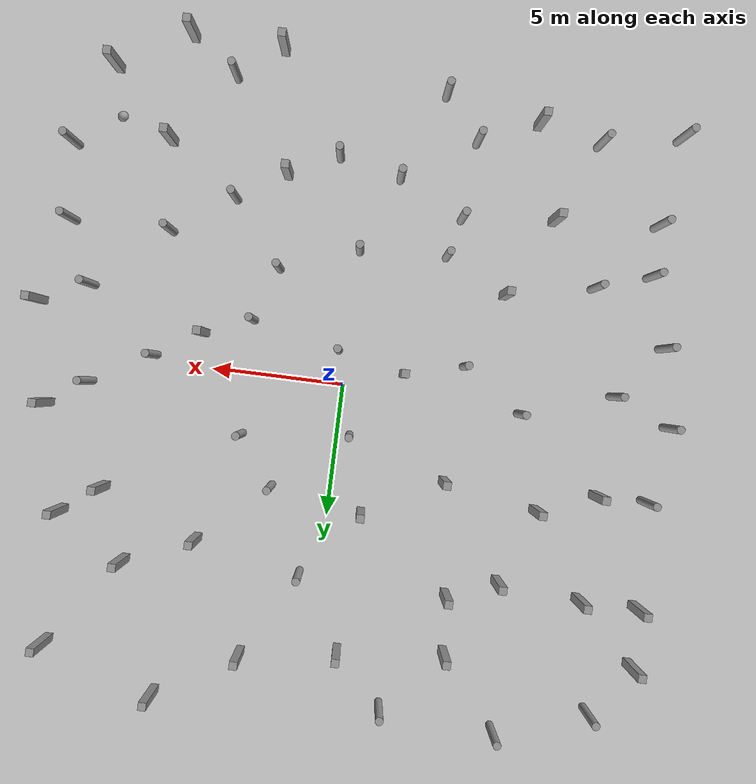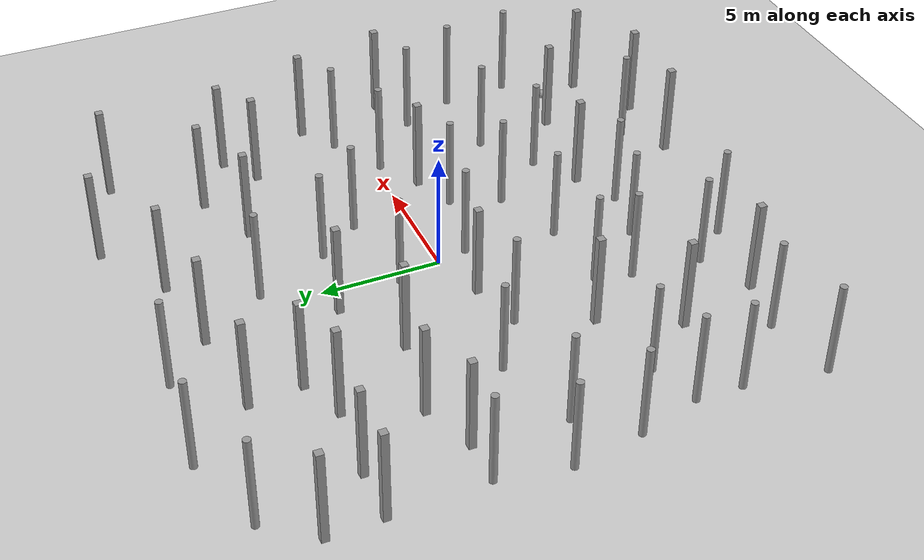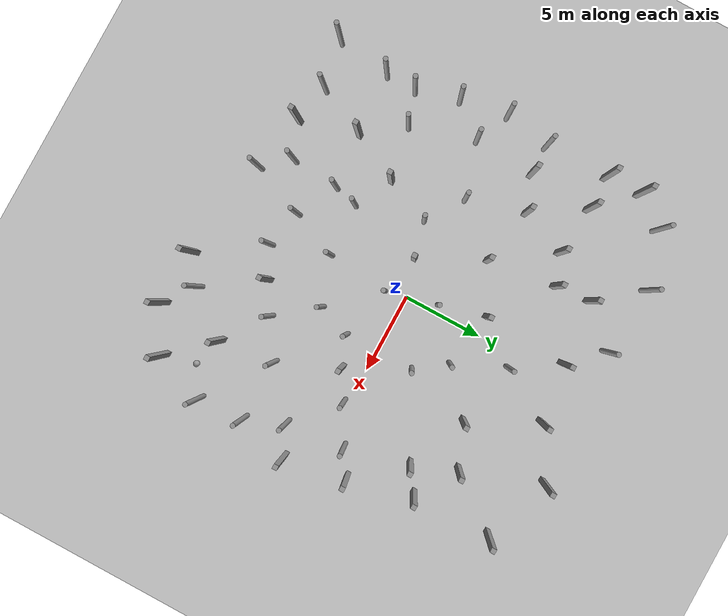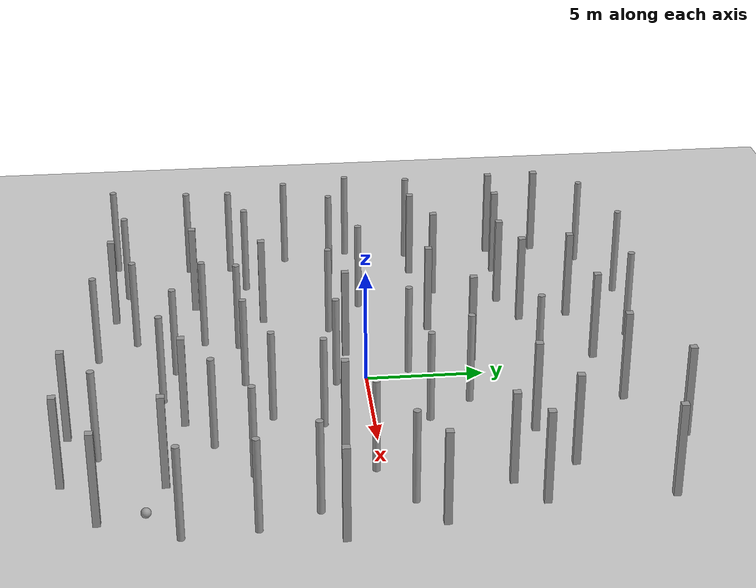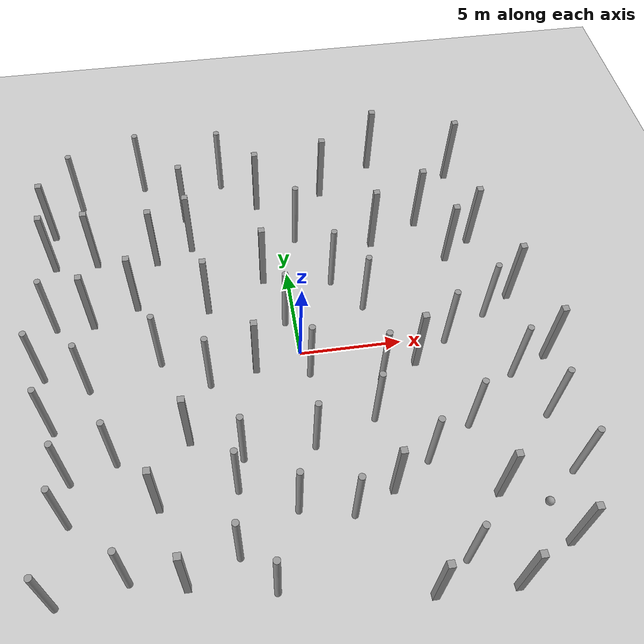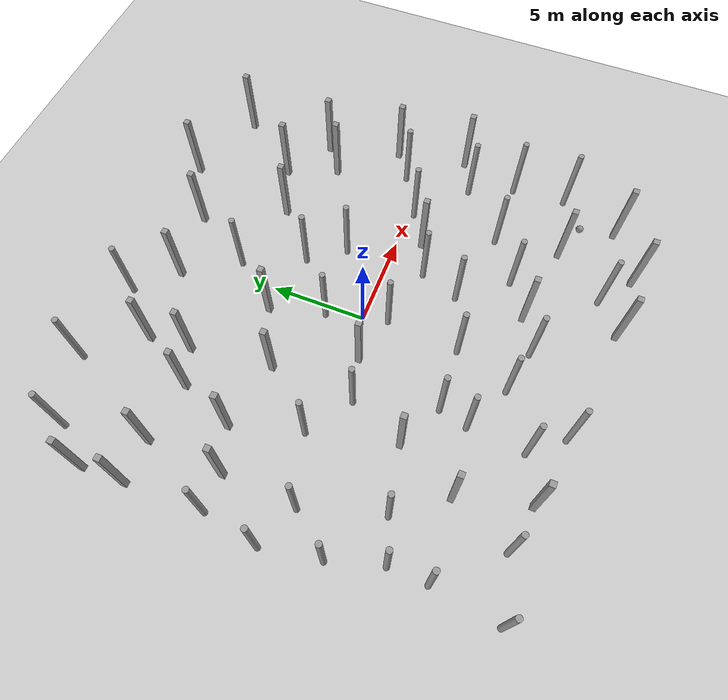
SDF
<sdf version="1.6">
 <world name="default">
  <light name="sun" type="directional">
   <pose>0 0 10 0 -0 0</pose>
   <diffuse>0.8 0.8 0.8 1</diffuse>
   <specular>0.2 0.2 0.2 1</specular>
   <attenuation>
    <range>1000</range>
    <constant>0.9</constant>
    <linear>0.01</linear>
    <quadratic>0.001</quadratic>
   </attenuation>
   <direction>-0.5 0.1 -0.9</direction>
  </light>
  <model name="ground_plane">
   <static>1</static>
   <link name="link">
    <collision name="collision">
     <geometry><plane><normal>0 0 1</normal><size>100 100</size></plane></geometry>
    </collision>
    <visual name="visual">
     <cast_shadows>0</cast_shadows>
     <geometry><plane><normal>0 0 1</normal><size>100 100</size></plane></geometry>
     <material>
      <script><uri>file://media/materials/scripts/gazebo.material</uri><name>Gazebo/Gray</name></script>
     </material>
    </visual>
   </link>
  </model>
  <gravity>0 0 -9.8</gravity>
  <magnetic_field>6e-06 2.3e-05 -4.2e-05</magnetic_field>
  <atmosphere type="adiabatic"/>
  <physics name="default_physics" default="0" type="ode">
   <max_step_size>0.002</max_step_size>
   <real_time_factor>1</real_time_factor>
   <real_time_update_rate>500</real_time_update_rate>
  </physics>
  <scene><ambient>0.4 0.4 0.4 1</ambient><background>0.7 0.7 0.7 1</background><shadows>1</shadows></scene>
  <spherical_coordinates>
   <surface_model>EARTH_WGS84</surface_model>
   <latitude_deg>0</latitude_deg>
   <longitude_deg>0</longitude_deg>
   <elevation>0</elevation>
   <heading_deg>0</heading_deg>
  </spherical_coordinates>
  <model name="unit_sphere">
   <link name="link">
    <inertial>
     <mass>1</mass>
     <inertia><ixx>0.1</ixx><ixy>0</ixy><ixz>0</ixz><iyy>0.1</iyy><iyz>0</iyz><izz>0.1</izz></inertia>
    </inertial>
    <gravity>0</gravity>
    <visual name="visual">
     <geometry><sphere><radius>0.203941</radius></sphere></geometry>
     <material>
      <script><name>Gazebo/Grey</name><uri>file://media/materials/scripts/gazebo.material</uri></script>
      <shader type="pixel"><normal_map>__default__</normal_map></shader>
     </material>
    </visual>
    <collision name="collision">
     <geometry><sphere><radius>0.203941</radius></sphere></geometry>
     <surface>
      <friction>
       <ode><mu>1</mu><mu2>1</mu2><fdir1>0 0 0</fdir1><slip1>0</slip1><slip2>0</slip2></ode>
       <torsional>
        <coefficient>1</coefficient>
        <patch_radius>0</patch_radius>
        <surface_radius>0</surface_radius>
        <use_patch_radius>1</use_patch_radius>
        <ode><slip>0</slip></ode>
       </torsional>
      </friction>
      <bounce><restitution_coefficient>0</restitution_coefficient><threshold>1e+06</threshold></bounce>
      <contact>
       <collide_without_contact>0</collide_without_contact>
       <collide_without_contact_bitmask>1</collide_without_contact_bitmask>
       <collide_bitmask>1</collide_bitmask>
       <ode>
        <soft_cfm>0</soft_cfm>
        <soft_erp>0.2</soft_erp>
        <kp>1e+13</kp>
        <kd>1</kd>
        <max_vel>0.01</max_vel>
        <min_depth>0</min_depth>
       </ode>
       <bullet>
        <split_impulse>1</split_impulse>
        <split_impulse_penetration_threshold>-0.01</split_impulse_penetration_threshold>
        <soft_cfm>0</soft_cfm>
        <soft_erp>0.2</soft_erp>
        <kp>1e+13</kp>
        <kd>1</kd>
       </bullet>
      </contact>
     </surface>
    </collision>
   </link>
   <static>0</static>
   <pose>9.54607 -9.14462 0.203941 0 -0 0</pose>
  </model>
  <audio><device>default</device></audio>
  <model name="unit_box">
   <link name="link">
    <inertial>
     <mass>1000</mass>
     <inertia><ixx>166.667</ixx><ixy>0</ixy><ixz>0</ixz><iyy>166.667</iyy><iyz>0</iyz><izz>166.667</izz></inertia>
    </inertial>
    <visual name="visual">
     <geometry><box><size>0.3 0.3 4</size></box></geometry>
     <material>
      <script><name>Gazebo/Grey</name><uri>file://media/materials/scripts/gazebo.material</uri></script>
      <shader type="vertex"><normal_map>__default__</normal_map></shader>
      <ambient>0.3 0.3 0.3 1</ambient>
      <diffuse>0.7 0.7 0.7 1</diffuse>
      <specular>0.01 0.01 0.01 1</specular>
      <emissive>0 0 0 1</emissive>
     </material>
    </visual>
    <collision name="collision">
     <geometry><box><size>0.3 0.3 4</size></box></geometry>
     <surface>
      <friction>
       <ode><mu>1</mu><mu2>1</mu2><fdir1>0 0 0</fdir1><slip1>0</slip1><slip2>0</slip2></ode>
       <torsional>
        <coefficient>1</coefficient>
        <patch_radius>0</patch_radius>
        <surface_radius>0</surface_radius>
        <use_patch_radius>1</use_patch_radius>
        <ode><slip>0</slip></ode>
       </torsional>
      </friction>
      <bounce><restitution_coefficient>0</restitution_coefficient><threshold>1e+06</threshold></bounce>
      <contact>
       <collide_without_contact>0</collide_without_contact>
       <collide_without_contact_bitmask>1</collide_without_contact_bitmask>
       <collide_bitmask>1</collide_bitmask>
       <ode>
        <soft_cfm>0</soft_cfm>
        <soft_erp>0.2</soft_erp>
        <kp>1e+13</kp>
        <kd>1</kd>
        <max_vel>0.01</max_vel>
        <min_depth>0</min_depth>
       </ode>
       <bullet>
        <split_impulse>1</split_impulse>
        <split_impulse_penetration_threshold>-0.01</split_impulse_penetration_threshold>
        <soft_cfm>0</soft_cfm>
        <soft_erp>0.2</soft_erp>
        <kp>1e+13</kp>
        <kd>1</kd>
       </bullet>
      </contact>
     </surface>
    </collision>
   </link>
   <static>0</static>
   <pose>-1.26731 4.71521 2 1e-05 1e-06 -0.00411</pose>
  </model>
  <model name="unit_box_clone">
   <link name="link">
    <inertial>
     <mass>1000</mass>
     <inertia><ixx>166.667</ixx><ixy>0</ixy><ixz>0</ixz><iyy>166.667</iyy><iyz>0</iyz><izz>166.667</izz></inertia>
    </inertial>
    <visual name="visual">
     <geometry><box><size>0.3 0.3 4</size></box></geometry>
     <material>
      <script><name>Gazebo/Grey</name><uri>file://media/materials/scripts/gazebo.material</uri></script>
      <shader type="vertex"><normal_map>__default__</normal_map></shader>
      <ambient>0.3 0.3 0.3 1</ambient>
      <diffuse>0.7 0.7 0.7 1</diffuse>
      <specular>0.01 0.01 0.01 1</specular>
      <emissive>0 0 0 1</emissive>
     </material>
    </visual>
    <collision name="collision">
     <geometry><box><size>0.3 0.3 4</size></box></geometry>
     <surface>
      <friction>
       <ode><mu>1</mu><mu2>1</mu2><fdir1>0 0 0</fdir1><slip1>0</slip1><slip2>0</slip2></ode>
       <torsional>
        <coefficient>1</coefficient>
        <patch_radius>0</patch_radius>
        <surface_radius>0</surface_radius>
        <use_patch_radius>1</use_patch_radius>
        <ode><slip>0</slip></ode>
       </torsional>
      </friction>
      <bounce><restitution_coefficient>0</restitution_coefficient><threshold>1e+06</threshold></bounce>
      <contact>
       <collide_without_contact>0</collide_without_contact>
       <collide_without_contact_bitmask>1</collide_without_contact_bitmask>
       <collide_bitmask>1</collide_bitmask>
       <ode>
        <soft_cfm>0</soft_cfm>
        <soft_erp>0.2</soft_erp>
        <kp>1e+13</kp>
        <kd>1</kd>
        <max_vel>0.01</max_vel>
        <min_depth>0</min_depth>
       </ode>
       <bullet>
        <split_impulse>1</split_impulse>
        <split_impulse_penetration_threshold>-0.01</split_impulse_penetration_threshold>
        <soft_cfm>0</soft_cfm>
        <soft_erp>0.2</soft_erp>
        <kp>1e+13</kp>
        <kd>1</kd>
       </bullet>
      </contact>
     </surface>
    </collision>
   </link>
   <static>0</static>
   <pose>-2.25021 -0.681029 2 1e-06 -4e-06 -0.005446</pose>
  </model>
  <model name="unit_box_clone_3">
   <link name="link">
    <inertial>
     <mass>1000</mass>
     <inertia><ixx>166.667</ixx><ixy>0</ixy><ixz>0</ixz><iyy>166.667</iyy><iyz>0</iyz><izz>166.667</izz></inertia>
    </inertial>
    <visual name="visual">
     <geometry><box><size>0.3 0.3 4</size></box></geometry>
     <material>
      <script><name>Gazebo/Grey</name><uri>file://media/materials/scripts/gazebo.material</uri></script>
      <shader type="vertex"><normal_map>__default__</normal_map></shader>
      <ambient>0.3 0.3 0.3 1</ambient>
      <diffuse>0.7 0.7 0.7 1</diffuse>
      <specular>0.01 0.01 0.01 1</specular>
      <emissive>0 0 0 1</emissive>
     </material>
    </visual>
    <collision name="collision">
     <geometry><box><size>0.3 0.3 4</size></box></geometry>
     <surface>
      <friction>
       <ode><mu>1</mu><mu2>1</mu2><fdir1>0 0 0</fdir1><slip1>0</slip1><slip2>0</slip2></ode>
       <torsional>
        <coefficient>1</coefficient>
        <patch_radius>0</patch_radius>
        <surface_radius>0</surface_radius>
        <use_patch_radius>1</use_patch_radius>
        <ode><slip>0</slip></ode>
       </torsional>
      </friction>
      <bounce><restitution_coefficient>0</restitution_coefficient><threshold>1e+06</threshold></bounce>
      <contact>
       <collide_without_contact>0</collide_without_contact>
       <collide_without_contact_bitmask>1</collide_without_contact_bitmask>
       <collide_bitmask>1</collide_bitmask>
       <ode>
        <soft_cfm>0</soft_cfm>
        <soft_erp>0.2</soft_erp>
        <kp>1e+13</kp>
        <kd>1</kd>
        <max_vel>0.01</max_vel>
        <min_depth>0</min_depth>
       </ode>
       <bullet>
        <split_impulse>1</split_impulse>
        <split_impulse_penetration_threshold>-0.01</split_impulse_penetration_threshold>
        <soft_cfm>0</soft_cfm>
        <soft_erp>0.2</soft_erp>
        <kp>1e+13</kp>
        <kd>1</kd>
       </bullet>
      </contact>
     </surface>
    </collision>
   </link>
   <static>0</static>
   <pose>-9.81581 6.97361 2 5e-06 1e-06 -0.004296</pose>
  </model>
  <model name="unit_box_clone_4">
   <link name="link">
    <inertial>
     <mass>1000</mass>
     <inertia><ixx>166.667</ixx><ixy>0</ixy><ixz>0</ixz><iyy>166.667</iyy><iyz>0</iyz><izz>166.667</izz></inertia>
    </inertial>
    <visual name="visual">
     <geometry><box><size>0.3 0.3 4</size></box></geometry>
     <material>
      <script><name>Gazebo/Grey</name><uri>file://media/materials/scripts/gazebo.material</uri></script>
      <shader type="vertex"><normal_map>__default__</normal_map></shader>
      <ambient>0.3 0.3 0.3 1</ambient>
      <diffuse>0.7 0.7 0.7 1</diffuse>
      <specular>0.01 0.01 0.01 1</specular>
      <emissive>0 0 0 1</emissive>
     </material>
    </visual>
    <collision name="collision">
     <geometry><box><size>0.3 0.3 4</size></box></geometry>
     <surface>
      <friction>
       <ode><mu>1</mu><mu2>1</mu2><fdir1>0 0 0</fdir1><slip1>0</slip1><slip2>0</slip2></ode>
       <torsional>
        <coefficient>1</coefficient>
        <patch_radius>0</patch_radius>
        <surface_radius>0</surface_radius>
        <use_patch_radius>1</use_patch_radius>
        <ode><slip>0</slip></ode>
       </torsional>
      </friction>
      <bounce><restitution_coefficient>0</restitution_coefficient><threshold>1e+06</threshold></bounce>
      <contact>
       <collide_without_contact>0</collide_without_contact>
       <collide_without_contact_bitmask>1</collide_without_contact_bitmask>
       <collide_bitmask>1</collide_bitmask>
       <ode>
        <soft_cfm>0</soft_cfm>
        <soft_erp>0.2</soft_erp>
        <kp>1e+13</kp>
        <kd>1</kd>
        <max_vel>0.01</max_vel>
        <min_depth>0</min_depth>
       </ode>
       <bullet>
        <split_impulse>1</split_impulse>
        <split_impulse_penetration_threshold>-0.01</split_impulse_penetration_threshold>
        <soft_cfm>0</soft_cfm>
        <soft_erp>0.2</soft_erp>
        <kp>1e+13</kp>
        <kd>1</kd>
       </bullet>
      </contact>
     </surface>
    </collision>
   </link>
   <static>0</static>
   <pose>-12.064 9.20919 2 -8e-06 2e-06 -0.002625</pose>
  </model>
  <model name="unit_box_clone_7">
   <link name="link">
    <inertial>
     <mass>1000</mass>
     <inertia><ixx>166.667</ixx><ixy>0</ixy><ixz>0</ixz><iyy>166.667</iyy><iyz>0</iyz><izz>166.667</izz></inertia>
    </inertial>
    <visual name="visual">
     <geometry><box><size>0.3 0.3 4</size></box></geometry>
     <material>
      <script><name>Gazebo/Grey</name><uri>file://media/materials/scripts/gazebo.material</uri></script>
      <shader type="vertex"><normal_map>__default__</normal_map></shader>
      <ambient>0.3 0.3 0.3 1</ambient>
      <diffuse>0.7 0.7 0.7 1</diffuse>
      <specular>0.01 0.01 0.01 1</specular>
      <emissive>0 0 0 1</emissive>
     </material>
    </visual>
    <collision name="collision">
     <geometry><box><size>0.3 0.3 4</size></box></geometry>
     <surface>
      <friction>
       <ode><mu>1</mu><mu2>1</mu2><fdir1>0 0 0</fdir1><slip1>0</slip1><slip2>0</slip2></ode>
       <torsional>
        <coefficient>1</coefficient>
        <patch_radius>0</patch_radius>
        <surface_radius>0</surface_radius>
        <use_patch_radius>1</use_patch_radius>
        <ode><slip>0</slip></ode>
       </torsional>
      </friction>
      <bounce><restitution_coefficient>0</restitution_coefficient><threshold>1e+06</threshold></bounce>
      <contact>
       <collide_without_contact>0</collide_without_contact>
       <collide_without_contact_bitmask>1</collide_without_contact_bitmask>
       <collide_bitmask>1</collide_bitmask>
       <ode>
        <soft_cfm>0</soft_cfm>
        <soft_erp>0.2</soft_erp>
        <kp>1e+13</kp>
        <kd>1</kd>
        <max_vel>0.01</max_vel>
        <min_depth>0</min_depth>
       </ode>
       <bullet>
        <split_impulse>1</split_impulse>
        <split_impulse_penetration_threshold>-0.01</split_impulse_penetration_threshold>
        <soft_cfm>0</soft_cfm>
        <soft_erp>0.2</soft_erp>
        <kp>1e+13</kp>
        <kd>1</kd>
       </bullet>
      </contact>
     </surface>
    </collision>
   </link>
   <static>0</static>
   <pose>9.86054 -10.9628 2.00001 -4.1e-05 -2e-06 -0.008062</pose>
  </model>
  <model name="unit_box_clone_8">
   <link name="link">
    <inertial>
     <mass>1000</mass>
     <inertia><ixx>166.667</ixx><ixy>0</ixy><ixz>0</ixz><iyy>166.667</iyy><iyz>0</iyz><izz>166.667</izz></inertia>
    </inertial>
    <visual name="visual">
     <geometry><box><size>0.3 0.3 4</size></box></geometry>
     <material>
      <script><name>Gazebo/Grey</name><uri>file://media/materials/scripts/gazebo.material</uri></script>
      <shader type="vertex"><normal_map>__default__</normal_map></shader>
      <ambient>0.3 0.3 0.3 1</ambient>
      <diffuse>0.7 0.7 0.7 1</diffuse>
      <specular>0.01 0.01 0.01 1</specular>
      <emissive>0 0 0 1</emissive>
     </material>
    </visual>
    <collision name="collision">
     <geometry><box><size>0.3 0.3 4</size></box></geometry>
     <surface>
      <friction>
       <ode><mu>1</mu><mu2>1</mu2><fdir1>0 0 0</fdir1><slip1>0</slip1><slip2>0</slip2></ode>
       <torsional>
        <coefficient>1</coefficient>
        <patch_radius>0</patch_radius>
        <surface_radius>0</surface_radius>
        <use_patch_radius>1</use_patch_radius>
        <ode><slip>0</slip></ode>
       </torsional>
      </friction>
      <bounce><restitution_coefficient>0</restitution_coefficient><threshold>1e+06</threshold></bounce>
      <contact>
       <collide_without_contact>0</collide_without_contact>
       <collide_without_contact_bitmask>1</collide_without_contact_bitmask>
       <collide_bitmask>1</collide_bitmask>
       <ode>
        <soft_cfm>0</soft_cfm>
        <soft_erp>0.2</soft_erp>
        <kp>1e+13</kp>
        <kd>1</kd>
        <max_vel>0.01</max_vel>
        <min_depth>0</min_depth>
       </ode>
       <bullet>
        <split_impulse>1</split_impulse>
        <split_impulse_penetration_threshold>-0.01</split_impulse_penetration_threshold>
        <soft_cfm>0</soft_cfm>
        <soft_erp>0.2</soft_erp>
        <kp>1e+13</kp>
        <kd>1</kd>
       </bullet>
      </contact>
     </surface>
    </collision>
   </link>
   <static>0</static>
   <pose>-6.68885 6.67572 2 -3e-06 2.3e-05 0.003441</pose>
  </model>
  <model name="unit_box_clone_13">
   <link name="link">
    <inertial>
     <mass>1000</mass>
     <inertia><ixx>166.667</ixx><ixy>0</ixy><ixz>0</ixz><iyy>166.667</iyy><iyz>0</iyz><izz>166.667</izz></inertia>
    </inertial>
    <visual name="visual">
     <geometry><box><size>0.3 0.3 4</size></box></geometry>
     <material>
      <script><name>Gazebo/Grey</name><uri>file://media/materials/scripts/gazebo.material</uri></script>
      <shader type="vertex"><normal_map>__default__</normal_map></shader>
      <ambient>0.3 0.3 0.3 1</ambient>
      <diffuse>0.7 0.7 0.7 1</diffuse>
      <specular>0.01 0.01 0.01 1</specular>
      <emissive>0 0 0 1</emissive>
     </material>
    </visual>
    <collision name="collision">
     <geometry><box><size>0.3 0.3 4</size></box></geometry>
     <surface>
      <friction>
       <ode><mu>1</mu><mu2>1</mu2><fdir1>0 0 0</fdir1><slip1>0</slip1><slip2>0</slip2></ode>
       <torsional>
        <coefficient>1</coefficient>
        <patch_radius>0</patch_radius>
        <surface_radius>0</surface_radius>
        <use_patch_radius>1</use_patch_radius>
        <ode><slip>0</slip></ode>
       </torsional>
      </friction>
      <bounce><restitution_coefficient>0</restitution_coefficient><threshold>1e+06</threshold></bounce>
      <contact>
       <collide_without_contact>0</collide_without_contact>
       <collide_without_contact_bitmask>1</collide_without_contact_bitmask>
       <collide_bitmask>1</collide_bitmask>
       <ode>
        <soft_cfm>0</soft_cfm>
        <soft_erp>0.2</soft_erp>
        <kp>1e+13</kp>
        <kd>1</kd>
        <max_vel>0.01</max_vel>
        <min_depth>0</min_depth>
       </ode>
       <bullet>
        <split_impulse>1</split_impulse>
        <split_impulse_penetration_threshold>-0.01</split_impulse_penetration_threshold>
        <soft_cfm>0</soft_cfm>
        <soft_erp>0.2</soft_erp>
        <kp>1e+13</kp>
        <kd>1</kd>
       </bullet>
      </contact>
     </surface>
    </collision>
   </link>
   <static>0</static>
   <pose>-10.0001 3.00009 2 -7e-06 2e-06 -0.000104</pose>
  </model>
  <model name="unit_box_clone_14">
   <link name="link">
    <inertial>
     <mass>1000</mass>
     <inertia><ixx>166.667</ixx><ixy>0</ixy><ixz>0</ixz><iyy>166.667</iyy><iyz>0</iyz><izz>166.667</izz></inertia>
    </inertial>
    <visual name="visual">
     <geometry><box><size>0.3 0.3 4</size></box></geometry>
     <material>
      <script><name>Gazebo/Grey</name><uri>file://media/materials/scripts/gazebo.material</uri></script>
      <shader type="vertex"><normal_map>__default__</normal_map></shader>
      <ambient>0.3 0.3 0.3 1</ambient>
      <diffuse>0.7 0.7 0.7 1</diffuse>
      <specular>0.01 0.01 0.01 1</specular>
      <emissive>0 0 0 1</emissive>
     </material>
    </visual>
    <collision name="collision">
     <geometry><box><size>0.3 0.3 4</size></box></geometry>
     <surface>
      <friction>
       <ode><mu>1</mu><mu2>1</mu2><fdir1>0 0 0</fdir1><slip1>0</slip1><slip2>0</slip2></ode>
       <torsional>
        <coefficient>1</coefficient>
        <patch_radius>0</patch_radius>
        <surface_radius>0</surface_radius>
        <use_patch_radius>1</use_patch_radius>
        <ode><slip>0</slip></ode>
       </torsional>
      </friction>
      <bounce><restitution_coefficient>0</restitution_coefficient><threshold>1e+06</threshold></bounce>
      <contact>
       <collide_without_contact>0</collide_without_contact>
       <collide_without_contact_bitmask>1</collide_without_contact_bitmask>
       <collide_bitmask>1</collide_bitmask>
       <ode>
        <soft_cfm>0</soft_cfm>
        <soft_erp>0.2</soft_erp>
        <kp>1e+13</kp>
        <kd>1</kd>
        <max_vel>0.01</max_vel>
        <min_depth>0</min_depth>
       </ode>
       <bullet>
        <split_impulse>1</split_impulse>
        <split_impulse_penetration_threshold>-0.01</split_impulse_penetration_threshold>
        <soft_cfm>0</soft_cfm>
        <soft_erp>0.2</soft_erp>
        <kp>1e+13</kp>
        <kd>1</kd>
       </bullet>
      </contact>
     </surface>
    </collision>
   </link>
   <static>0</static>
   <pose>-11.9999 7.00011 2 -0 -1e-06 0.000133</pose>
  </model>
  <model name="unit_box_clone_22">
   <link name="link">
    <inertial>
     <mass>1000</mass>
     <inertia><ixx>166.667</ixx><ixy>0</ixy><ixz>0</ixz><iyy>166.667</iyy><iyz>0</iyz><izz>166.667</izz></inertia>
    </inertial>
    <visual name="visual">
     <geometry><box><size>0.3 0.3 4</size></box></geometry>
     <material>
      <script><name>Gazebo/Grey</name><uri>file://media/materials/scripts/gazebo.material</uri></script>
      <shader type="vertex"><normal_map>__default__</normal_map></shader>
      <ambient>0.3 0.3 0.3 1</ambient>
      <diffuse>0.7 0.7 0.7 1</diffuse>
      <specular>0.01 0.01 0.01 1</specular>
      <emissive>0 0 0 1</emissive>
     </material>
    </visual>
    <collision name="collision">
     <geometry><box><size>0.3 0.3 4</size></box></geometry>
     <surface>
      <friction>
       <ode><mu>1</mu><mu2>1</mu2><fdir1>0 0 0</fdir1><slip1>0</slip1><slip2>0</slip2></ode>
       <torsional>
        <coefficient>1</coefficient>
        <patch_radius>0</patch_radius>
        <surface_radius>0</surface_radius>
        <use_patch_radius>1</use_patch_radius>
        <ode><slip>0</slip></ode>
       </torsional>
      </friction>
      <bounce><restitution_coefficient>0</restitution_coefficient><threshold>1e+06</threshold></bounce>
      <contact>
       <collide_without_contact>0</collide_without_contact>
       <collide_without_contact_bitmask>1</collide_without_contact_bitmask>
       <collide_bitmask>1</collide_bitmask>
       <ode>
        <soft_cfm>0</soft_cfm>
        <soft_erp>0.2</soft_erp>
        <kp>1e+13</kp>
        <kd>1</kd>
        <max_vel>0.01</max_vel>
        <min_depth>0</min_depth>
       </ode>
       <bullet>
        <split_impulse>1</split_impulse>
        <split_impulse_penetration_threshold>-0.01</split_impulse_penetration_threshold>
        <soft_cfm>0</soft_cfm>
        <soft_erp>0.2</soft_erp>
        <kp>1e+13</kp>
        <kd>1</kd>
       </bullet>
      </contact>
     </surface>
    </collision>
   </link>
   <static>0</static>
   <pose>-0.999877 9.99992 2 1.3e-05 -4e-06 -0.007695</pose>
  </model>
  <model name="unit_box_clone_23">
   <link name="link">
    <inertial>
     <mass>1000</mass>
     <inertia><ixx>166.667</ixx><ixy>0</ixy><ixz>0</ixz><iyy>166.667</iyy><iyz>0</iyz><izz>166.667</izz></inertia>
    </inertial>
    <visual name="visual">
     <geometry><box><size>0.3 0.3 4</size></box></geometry>
     <material>
      <script><name>Gazebo/Grey</name><uri>file://media/materials/scripts/gazebo.material</uri></script>
      <shader type="vertex"><normal_map>__default__</normal_map></shader>
      <ambient>0.3 0.3 0.3 1</ambient>
      <diffuse>0.7 0.7 0.7 1</diffuse>
      <specular>0.01 0.01 0.01 1</specular>
      <emissive>0 0 0 1</emissive>
     </material>
    </visual>
    <collision name="collision">
     <geometry><box><size>0.3 0.3 4</size></box></geometry>
     <surface>
      <friction>
       <ode><mu>1</mu><mu2>1</mu2><fdir1>0 0 0</fdir1><slip1>0</slip1><slip2>0</slip2></ode>
       <torsional>
        <coefficient>1</coefficient>
        <patch_radius>0</patch_radius>
        <surface_radius>0</surface_radius>
        <use_patch_radius>1</use_patch_radius>
        <ode><slip>0</slip></ode>
       </torsional>
      </friction>
      <bounce><restitution_coefficient>0</restitution_coefficient><threshold>1e+06</threshold></bounce>
      <contact>
       <collide_without_contact>0</collide_without_contact>
       <collide_without_contact_bitmask>1</collide_without_contact_bitmask>
       <collide_bitmask>1</collide_bitmask>
       <ode>
        <soft_cfm>0</soft_cfm>
        <soft_erp>0.2</soft_erp>
        <kp>1e+13</kp>
        <kd>1</kd>
        <max_vel>0.01</max_vel>
        <min_depth>0</min_depth>
       </ode>
       <bullet>
        <split_impulse>1</split_impulse>
        <split_impulse_penetration_threshold>-0.01</split_impulse_penetration_threshold>
        <soft_cfm>0</soft_cfm>
        <soft_erp>0.2</soft_erp>
        <kp>1e+13</kp>
        <kd>1</kd>
       </bullet>
      </contact>
     </surface>
    </collision>
   </link>
   <static>0</static>
   <pose>-5.00228 9.5919 2 0 -0 0.000109</pose>
  </model>
  <model name="unit_box_clone_24">
   <link name="link">
    <inertial>
     <mass>1000</mass>
     <inertia><ixx>166.667</ixx><ixy>0</ixy><ixz>0</ixz><iyy>166.667</iyy><iyz>0</iyz><izz>166.667</izz></inertia>
    </inertial>
    <visual name="visual">
     <geometry><box><size>0.3 0.3 4</size></box></geometry>
     <material>
      <script><name>Gazebo/Grey</name><uri>file://media/materials/scripts/gazebo.material</uri></script>
      <shader type="vertex"><normal_map>__default__</normal_map></shader>
      <ambient>0.3 0.3 0.3 1</ambient>
      <diffuse>0.7 0.7 0.7 1</diffuse>
      <specular>0.01 0.01 0.01 1</specular>
      <emissive>0 0 0 1</emissive>
     </material>
    </visual>
    <collision name="collision">
     <geometry><box><size>0.3 0.3 4</size></box></geometry>
     <surface>
      <friction>
       <ode><mu>1</mu><mu2>1</mu2><fdir1>0 0 0</fdir1><slip1>0</slip1><slip2>0</slip2></ode>
       <torsional>
        <coefficient>1</coefficient>
        <patch_radius>0</patch_radius>
        <surface_radius>0</surface_radius>
        <use_patch_radius>1</use_patch_radius>
        <ode><slip>0</slip></ode>
       </torsional>
      </friction>
      <bounce><restitution_coefficient>0</restitution_coefficient><threshold>1e+06</threshold></bounce>
      <contact>
       <collide_without_contact>0</collide_without_contact>
       <collide_without_contact_bitmask>1</collide_without_contact_bitmask>
       <collide_bitmask>1</collide_bitmask>
       <ode>
        <soft_cfm>0</soft_cfm>
        <soft_erp>0.2</soft_erp>
        <kp>1e+13</kp>
        <kd>1</kd>
        <max_vel>0.01</max_vel>
        <min_depth>0</min_depth>
       </ode>
       <bullet>
        <split_impulse>1</split_impulse>
        <split_impulse_penetration_threshold>-0.01</split_impulse_penetration_threshold>
        <soft_cfm>0</soft_cfm>
        <soft_erp>0.2</soft_erp>
        <kp>1e+13</kp>
        <kd>1</kd>
       </bullet>
      </contact>
     </surface>
    </collision>
   </link>
   <static>0</static>
   <pose>-4.80941 7.40664 2 1e-06 1e-06 0.002489</pose>
  </model>
  <model name="unit_box_clone_28">
   <link name="link">
    <inertial>
     <mass>1000</mass>
     <inertia><ixx>166.667</ixx><ixy>0</ixy><ixz>0</ixz><iyy>166.667</iyy><iyz>0</iyz><izz>166.667</izz></inertia>
    </inertial>
    <visual name="visual">
     <geometry><box><size>0.3 0.3 4</size></box></geometry>
     <material>
      <script><name>Gazebo/Grey</name><uri>file://media/materials/scripts/gazebo.material</uri></script>
      <shader type="vertex"><normal_map>__default__</normal_map></shader>
      <ambient>0.3 0.3 0.3 1</ambient>
      <diffuse>0.7 0.7 0.7 1</diffuse>
      <specular>0.01 0.01 0.01 1</specular>
      <emissive>0 0 0 1</emissive>
     </material>
    </visual>
    <collision name="collision">
     <geometry><box><size>0.3 0.3 4</size></box></geometry>
     <surface>
      <friction>
       <ode><mu>1</mu><mu2>1</mu2><fdir1>0 0 0</fdir1><slip1>0</slip1><slip2>0</slip2></ode>
       <torsional>
        <coefficient>1</coefficient>
        <patch_radius>0</patch_radius>
        <surface_radius>0</surface_radius>
        <use_patch_radius>1</use_patch_radius>
        <ode><slip>0</slip></ode>
       </torsional>
      </friction>
      <bounce><restitution_coefficient>0</restitution_coefficient><threshold>1e+06</threshold></bounce>
      <contact>
       <collide_without_contact>0</collide_without_contact>
       <collide_without_contact_bitmask>1</collide_without_contact_bitmask>
       <collide_bitmask>1</collide_bitmask>
       <ode>
        <soft_cfm>0</soft_cfm>
        <soft_erp>0.2</soft_erp>
        <kp>1e+13</kp>
        <kd>1</kd>
        <max_vel>0.01</max_vel>
        <min_depth>0</min_depth>
       </ode>
       <bullet>
        <split_impulse>1</split_impulse>
        <split_impulse_penetration_threshold>-0.01</split_impulse_penetration_threshold>
        <soft_cfm>0</soft_cfm>
        <soft_erp>0.2</soft_erp>
        <kp>1e+13</kp>
        <kd>1</kd>
       </bullet>
      </contact>
     </surface>
    </collision>
   </link>
   <static>0</static>
   <pose>-7.80118 3.82479 2 1e-06 -1e-06 -0.004584</pose>
  </model>
  <model name="unit_cylinder">
   <link name="link">
    <inertial>
     <mass>1000</mass>
     <inertia><ixx>145.833</ixx><ixy>0</ixy><ixz>0</ixz><iyy>145.833</iyy><iyz>0</iyz><izz>125</izz></inertia>
    </inertial>
    <visual name="visual">
     <geometry><cylinder><radius>0.15</radius><length>4</length></cylinder></geometry>
     <material>
      <script><name>Gazebo/Grey</name><uri>file://media/materials/scripts/gazebo.material</uri></script>
      <shader type="vertex"><normal_map>__default__</normal_map></shader>
      <ambient>0.3 0.3 0.3 1</ambient>
      <diffuse>0.7 0.7 0.7 1</diffuse>
      <specular>0.01 0.01 0.01 1</specular>
      <emissive>0 0 0 1</emissive>
     </material>
    </visual>
    <collision name="collision">
     <geometry><cylinder><radius>0.15</radius><length>4</length></cylinder></geometry>
     <surface>
      <friction>
       <ode><mu>1</mu><mu2>1</mu2><fdir1>0 0 0</fdir1><slip1>0</slip1><slip2>0</slip2></ode>
       <torsional>
        <coefficient>1</coefficient>
        <patch_radius>0</patch_radius>
        <surface_radius>0</surface_radius>
        <use_patch_radius>1</use_patch_radius>
        <ode><slip>0</slip></ode>
       </torsional>
      </friction>
      <bounce><restitution_coefficient>0</restitution_coefficient><threshold>1e+06</threshold></bounce>
      <contact>
       <collide_without_contact>0</collide_without_contact>
       <collide_without_contact_bitmask>1</collide_without_contact_bitmask>
       <collide_bitmask>1</collide_bitmask>
       <ode>
        <soft_cfm>0</soft_cfm>
        <soft_erp>0.2</soft_erp>
        <kp>1e+13</kp>
        <kd>1</kd>
        <max_vel>0.01</max_vel>
        <min_depth>0</min_depth>
       </ode>
       <bullet>
        <split_impulse>1</split_impulse>
        <split_impulse_penetration_threshold>-0.01</split_impulse_penetration_threshold>
        <soft_cfm>0</soft_cfm>
        <soft_erp>0.2</soft_erp>
        <kp>1e+13</kp>
        <kd>1</kd>
       </bullet>
      </contact>
     </surface>
    </collision>
   </link>
   <static>0</static>
   <pose>3.55793 2.3032 1.99998 -2e-06 -0 -0.203119</pose>
  </model>
  <model name="unit_cylinder_clone_3">
   <link name="link">
    <inertial>
     <mass>1000</mass>
     <inertia><ixx>145.833</ixx><ixy>0</ixy><ixz>0</ixz><iyy>145.833</iyy><iyz>0</iyz><izz>125</izz></inertia>
    </inertial>
    <visual name="visual">
     <geometry><cylinder><radius>0.15</radius><length>4</length></cylinder></geometry>
     <material>
      <script><name>Gazebo/Grey</name><uri>file://media/materials/scripts/gazebo.material</uri></script>
      <shader type="vertex"><normal_map>__default__</normal_map></shader>
      <ambient>0.3 0.3 0.3 1</ambient>
      <diffuse>0.7 0.7 0.7 1</diffuse>
      <specular>0.01 0.01 0.01 1</specular>
      <emissive>0 0 0 1</emissive>
     </material>
    </visual>
    <collision name="collision">
     <geometry><cylinder><radius>0.15</radius><length>4</length></cylinder></geometry>
     <surface>
      <friction>
       <ode><mu>1</mu><mu2>1</mu2><fdir1>0 0 0</fdir1><slip1>0</slip1><slip2>0</slip2></ode>
       <torsional>
        <coefficient>1</coefficient>
        <patch_radius>0</patch_radius>
        <surface_radius>0</surface_radius>
        <use_patch_radius>1</use_patch_radius>
        <ode><slip>0</slip></ode>
       </torsional>
      </friction>
      <bounce><restitution_coefficient>0</restitution_coefficient><threshold>1e+06</threshold></bounce>
      <contact>
       <collide_without_contact>0</collide_without_contact>
       <collide_without_contact_bitmask>1</collide_without_contact_bitmask>
       <collide_bitmask>1</collide_bitmask>
       <ode>
        <soft_cfm>0</soft_cfm>
        <soft_erp>0.2</soft_erp>
        <kp>1e+13</kp>
        <kd>1</kd>
        <max_vel>0.01</max_vel>
        <min_depth>0</min_depth>
       </ode>
       <bullet>
        <split_impulse>1</split_impulse>
        <split_impulse_penetration_threshold>-0.01</split_impulse_penetration_threshold>
        <soft_cfm>0</soft_cfm>
        <soft_erp>0.2</soft_erp>
        <kp>1e+13</kp>
        <kd>1</kd>
       </bullet>
      </contact>
     </surface>
    </collision>
   </link>
   <static>0</static>
   <pose>0.764147 7.25692 1.99998 -1e-06 1e-06 -0.195597</pose>
  </model>
  <model name="unit_cylinder_clone_0_clone">
   <link name="link">
    <inertial>
     <mass>1000</mass>
     <inertia><ixx>145.833</ixx><ixy>0</ixy><ixz>0</ixz><iyy>145.833</iyy><iyz>0</iyz><izz>125</izz></inertia>
    </inertial>
    <visual name="visual">
     <geometry><cylinder><radius>0.15</radius><length>4</length></cylinder></geometry>
     <material>
      <script><name>Gazebo/Grey</name><uri>file://media/materials/scripts/gazebo.material</uri></script>
      <shader type="vertex"><normal_map>__default__</normal_map></shader>
      <ambient>0.3 0.3 0.3 1</ambient>
      <diffuse>0.7 0.7 0.7 1</diffuse>
      <specular>0.01 0.01 0.01 1</specular>
      <emissive>0 0 0 1</emissive>
     </material>
    </visual>
    <collision name="collision">
     <geometry><cylinder><radius>0.15</radius><length>4</length></cylinder></geometry>
     <surface>
      <friction>
       <ode><mu>1</mu><mu2>1</mu2><fdir1>0 0 0</fdir1><slip1>0</slip1><slip2>0</slip2></ode>
       <torsional>
        <coefficient>1</coefficient>
        <patch_radius>0</patch_radius>
        <surface_radius>0</surface_radius>
        <use_patch_radius>1</use_patch_radius>
        <ode><slip>0</slip></ode>
       </torsional>
      </friction>
      <bounce><restitution_coefficient>0</restitution_coefficient><threshold>1e+06</threshold></bounce>
      <contact>
       <collide_without_contact>0</collide_without_contact>
       <collide_without_contact_bitmask>1</collide_without_contact_bitmask>
       <collide_bitmask>1</collide_bitmask>
       <ode>
        <soft_cfm>0</soft_cfm>
        <soft_erp>0.2</soft_erp>
        <kp>1e+13</kp>
        <kd>1</kd>
        <max_vel>0.01</max_vel>
        <min_depth>0</min_depth>
       </ode>
       <bullet>
        <split_impulse>1</split_impulse>
        <split_impulse_penetration_threshold>-0.01</split_impulse_penetration_threshold>
        <soft_cfm>0</soft_cfm>
        <soft_erp>0.2</soft_erp>
        <kp>1e+13</kp>
        <kd>1</kd>
       </bullet>
      </contact>
     </surface>
    </collision>
   </link>
   <static>0</static>
   <pose>10.8485 -4.989 1.99998 -1e-06 -0 -0.173285</pose>
  </model>
  <model name="unit_cylinder_clone_1_clone">
   <link name="link">
    <inertial>
     <mass>1000</mass>
     <inertia><ixx>145.833</ixx><ixy>0</ixy><ixz>0</ixz><iyy>145.833</iyy><iyz>0</iyz><izz>125</izz></inertia>
    </inertial>
    <visual name="visual">
     <geometry><cylinder><radius>0.15</radius><length>4</length></cylinder></geometry>
     <material>
      <script><name>Gazebo/Grey</name><uri>file://media/materials/scripts/gazebo.material</uri></script>
      <shader type="vertex"><normal_map>__default__</normal_map></shader>
      <ambient>0.3 0.3 0.3 1</ambient>
      <diffuse>0.7 0.7 0.7 1</diffuse>
      <specular>0.01 0.01 0.01 1</specular>
      <emissive>0 0 0 1</emissive>
     </material>
    </visual>
    <collision name="collision">
     <geometry><cylinder><radius>0.15</radius><length>4</length></cylinder></geometry>
     <surface>
      <friction>
       <ode><mu>1</mu><mu2>1</mu2><fdir1>0 0 0</fdir1><slip1>0</slip1><slip2>0</slip2></ode>
       <torsional>
        <coefficient>1</coefficient>
        <patch_radius>0</patch_radius>
        <surface_radius>0</surface_radius>
        <use_patch_radius>1</use_patch_radius>
        <ode><slip>0</slip></ode>
       </torsional>
      </friction>
      <bounce><restitution_coefficient>0</restitution_coefficient><threshold>1e+06</threshold></bounce>
      <contact>
       <collide_without_contact>0</collide_without_contact>
       <collide_without_contact_bitmask>1</collide_without_contact_bitmask>
       <collide_bitmask>1</collide_bitmask>
       <ode>
        <soft_cfm>0</soft_cfm>
        <soft_erp>0.2</soft_erp>
        <kp>1e+13</kp>
        <kd>1</kd>
        <max_vel>0.01</max_vel>
        <min_depth>0</min_depth>
       </ode>
       <bullet>
        <split_impulse>1</split_impulse>
        <split_impulse_penetration_threshold>-0.01</split_impulse_penetration_threshold>
        <soft_cfm>0</soft_cfm>
        <soft_erp>0.2</soft_erp>
        <kp>1e+13</kp>
        <kd>1</kd>
       </bullet>
      </contact>
     </surface>
    </collision>
   </link>
   <static>0</static>
   <pose>-1.25701 -8.01539 1.99995 -0.000271 -2.8e-05 -0.895801</pose>
  </model>
  <model name="unit_cylinder_clone_1_clone_1">
   <link name="link">
    <inertial>
     <mass>1000</mass>
     <inertia><ixx>145.833</ixx><ixy>0</ixy><ixz>0</ixz><iyy>145.833</iyy><iyz>0</iyz><izz>125</izz></inertia>
    </inertial>
    <visual name="visual">
     <geometry><cylinder><radius>0.15</radius><length>4</length></cylinder></geometry>
     <material>
      <script><name>Gazebo/Grey</name><uri>file://media/materials/scripts/gazebo.material</uri></script>
      <shader type="vertex"><normal_map>__default__</normal_map></shader>
      <ambient>0.3 0.3 0.3 1</ambient>
      <diffuse>0.7 0.7 0.7 1</diffuse>
      <specular>0.01 0.01 0.01 1</specular>
      <emissive>0 0 0 1</emissive>
     </material>
    </visual>
    <collision name="collision">
     <geometry><cylinder><radius>0.15</radius><length>4</length></cylinder></geometry>
     <surface>
      <friction>
       <ode><mu>1</mu><mu2>1</mu2><fdir1>0 0 0</fdir1><slip1>0</slip1><slip2>0</slip2></ode>
       <torsional>
        <coefficient>1</coefficient>
        <patch_radius>0</patch_radius>
        <surface_radius>0</surface_radius>
        <use_patch_radius>1</use_patch_radius>
        <ode><slip>0</slip></ode>
       </torsional>
      </friction>
      <bounce><restitution_coefficient>0</restitution_coefficient><threshold>1e+06</threshold></bounce>
      <contact>
       <collide_without_contact>0</collide_without_contact>
       <collide_without_contact_bitmask>1</collide_without_contact_bitmask>
       <collide_bitmask>1</collide_bitmask>
       <ode>
        <soft_cfm>0</soft_cfm>
        <soft_erp>0.2</soft_erp>
        <kp>1e+13</kp>
        <kd>1</kd>
        <max_vel>0.01</max_vel>
        <min_depth>0</min_depth>
       </ode>
       <bullet>
        <split_impulse>1</split_impulse>
        <split_impulse_penetration_threshold>-0.01</split_impulse_penetration_threshold>
        <soft_cfm>0</soft_cfm>
        <soft_erp>0.2</soft_erp>
        <kp>1e+13</kp>
        <kd>1</kd>
       </bullet>
      </contact>
     </surface>
    </collision>
   </link>
   <static>0</static>
   <pose>-11.8335 -2.8104 1.99995 -0.000271 -2.9e-05 -0.902102</pose>
  </model>
  <model name="unit_cylinder_clone_1_clone_2">
   <link name="link">
    <inertial>
     <mass>1000</mass>
     <inertia><ixx>145.833</ixx><ixy>0</ixy><ixz>0</ixz><iyy>145.833</iyy><iyz>0</iyz><izz>125</izz></inertia>
    </inertial>
    <visual name="visual">
     <geometry><cylinder><radius>0.15</radius><length>4</length></cylinder></geometry>
     <material>
      <script><name>Gazebo/Grey</name><uri>file://media/materials/scripts/gazebo.material</uri></script>
      <shader type="vertex"><normal_map>__default__</normal_map></shader>
      <ambient>0.3 0.3 0.3 1</ambient>
      <diffuse>0.7 0.7 0.7 1</diffuse>
      <specular>0.01 0.01 0.01 1</specular>
      <emissive>0 0 0 1</emissive>
     </material>
    </visual>
    <collision name="collision">
     <geometry><cylinder><radius>0.15</radius><length>4</length></cylinder></geometry>
     <surface>
      <friction>
       <ode><mu>1</mu><mu2>1</mu2><fdir1>0 0 0</fdir1><slip1>0</slip1><slip2>0</slip2></ode>
       <torsional>
        <coefficient>1</coefficient>
        <patch_radius>0</patch_radius>
        <surface_radius>0</surface_radius>
        <use_patch_radius>1</use_patch_radius>
        <ode><slip>0</slip></ode>
       </torsional>
      </friction>
      <bounce><restitution_coefficient>0</restitution_coefficient><threshold>1e+06</threshold></bounce>
      <contact>
       <collide_without_contact>0</collide_without_contact>
       <collide_without_contact_bitmask>1</collide_without_contact_bitmask>
       <collide_bitmask>1</collide_bitmask>
       <ode>
        <soft_cfm>0</soft_cfm>
        <soft_erp>0.2</soft_erp>
        <kp>1e+13</kp>
        <kd>1</kd>
        <max_vel>0.01</max_vel>
        <min_depth>0</min_depth>
       </ode>
       <bullet>
        <split_impulse>1</split_impulse>
        <split_impulse_penetration_threshold>-0.01</split_impulse_penetration_threshold>
        <soft_cfm>0</soft_cfm>
        <soft_erp>0.2</soft_erp>
        <kp>1e+13</kp>
        <kd>1</kd>
       </bullet>
      </contact>
     </surface>
    </collision>
   </link>
   <static>0</static>
   <pose>-3.73083 -6.76311 1.99995 -0.000271 -2.8e-05 -0.89745</pose>
  </model>
  <model name="unit_cylinder_clone_1_clone_4">
   <link name="link">
    <inertial>
     <mass>1000</mass>
     <inertia><ixx>145.833</ixx><ixy>0</ixy><ixz>0</ixz><iyy>145.833</iyy><iyz>0</iyz><izz>125</izz></inertia>
    </inertial>
    <visual name="visual">
     <geometry><cylinder><radius>0.15</radius><length>4</length></cylinder></geometry>
     <material>
      <script><name>Gazebo/Grey</name><uri>file://media/materials/scripts/gazebo.material</uri></script>
      <shader type="vertex"><normal_map>__default__</normal_map></shader>
      <ambient>0.3 0.3 0.3 1</ambient>
      <diffuse>0.7 0.7 0.7 1</diffuse>
      <specular>0.01 0.01 0.01 1</specular>
      <emissive>0 0 0 1</emissive>
     </material>
    </visual>
    <collision name="collision">
     <geometry><cylinder><radius>0.15</radius><length>4</length></cylinder></geometry>
     <surface>
      <friction>
       <ode><mu>1</mu><mu2>1</mu2><fdir1>0 0 0</fdir1><slip1>0</slip1><slip2>0</slip2></ode>
       <torsional>
        <coefficient>1</coefficient>
        <patch_radius>0</patch_radius>
        <surface_radius>0</surface_radius>
        <use_patch_radius>1</use_patch_radius>
        <ode><slip>0</slip></ode>
       </torsional>
      </friction>
      <bounce><restitution_coefficient>0</restitution_coefficient><threshold>1e+06</threshold></bounce>
      <contact>
       <collide_without_contact>0</collide_without_contact>
       <collide_without_contact_bitmask>1</collide_without_contact_bitmask>
       <collide_bitmask>1</collide_bitmask>
       <ode>
        <soft_cfm>0</soft_cfm>
        <soft_erp>0.2</soft_erp>
        <kp>1e+13</kp>
        <kd>1</kd>
        <max_vel>0.01</max_vel>
        <min_depth>0</min_depth>
       </ode>
       <bullet>
        <split_impulse>1</split_impulse>
        <split_impulse_penetration_threshold>-0.01</split_impulse_penetration_threshold>
        <soft_cfm>0</soft_cfm>
        <soft_erp>0.2</soft_erp>
        <kp>1e+13</kp>
        <kd>1</kd>
       </bullet>
      </contact>
     </surface>
    </collision>
   </link>
   <static>0</static>
   <pose>-8.98905 -4.76141 1.99995 -0.000271 -3e-05 -0.904065</pose>
  </model>
  <model name="unit_cylinder_clone_1_clone_6">
   <link name="link">
    <inertial>
     <mass>1000</mass>
     <inertia><ixx>145.833</ixx><ixy>0</ixy><ixz>0</ixz><iyy>145.833</iyy><iyz>0</iyz><izz>125</izz></inertia>
    </inertial>
    <visual name="visual">
     <geometry><cylinder><radius>0.15</radius><length>4</length></cylinder></geometry>
     <material>
      <script><name>Gazebo/Grey</name><uri>file://media/materials/scripts/gazebo.material</uri></script>
      <shader type="vertex"><normal_map>__default__</normal_map></shader>
      <ambient>0.3 0.3 0.3 1</ambient>
      <diffuse>0.7 0.7 0.7 1</diffuse>
      <specular>0.01 0.01 0.01 1</specular>
      <emissive>0 0 0 1</emissive>
     </material>
    </visual>
    <collision name="collision">
     <geometry><cylinder><radius>0.15</radius><length>4</length></cylinder></geometry>
     <surface>
      <friction>
       <ode><mu>1</mu><mu2>1</mu2><fdir1>0 0 0</fdir1><slip1>0</slip1><slip2>0</slip2></ode>
       <torsional>
        <coefficient>1</coefficient>
        <patch_radius>0</patch_radius>
        <surface_radius>0</surface_radius>
        <use_patch_radius>1</use_patch_radius>
        <ode><slip>0</slip></ode>
       </torsional>
      </friction>
      <bounce><restitution_coefficient>0</restitution_coefficient><threshold>1e+06</threshold></bounce>
      <contact>
       <collide_without_contact>0</collide_without_contact>
       <collide_without_contact_bitmask>1</collide_without_contact_bitmask>
       <collide_bitmask>1</collide_bitmask>
       <ode>
        <soft_cfm>0</soft_cfm>
        <soft_erp>0.2</soft_erp>
        <kp>1e+13</kp>
        <kd>1</kd>
        <max_vel>0.01</max_vel>
        <min_depth>0</min_depth>
       </ode>
       <bullet>
        <split_impulse>1</split_impulse>
        <split_impulse_penetration_threshold>-0.01</split_impulse_penetration_threshold>
        <soft_cfm>0</soft_cfm>
        <soft_erp>0.2</soft_erp>
        <kp>1e+13</kp>
        <kd>1</kd>
       </bullet>
      </contact>
     </surface>
    </collision>
   </link>
   <static>0</static>
   <pose>-3.34464 -5.28283 1.99998 -1e-06 -0 -0.211139</pose>
  </model>
  <model name="unit_cylinder_clone_1_clone_8">
   <link name="link">
    <inertial>
     <mass>1000</mass>
     <inertia><ixx>145.833</ixx><ixy>0</ixy><ixz>0</ixz><iyy>145.833</iyy><iyz>0</iyz><izz>125</izz></inertia>
    </inertial>
    <visual name="visual">
     <geometry><cylinder><radius>0.15</radius><length>4</length></cylinder></geometry>
     <material>
      <script><name>Gazebo/Grey</name><uri>file://media/materials/scripts/gazebo.material</uri></script>
      <shader type="vertex"><normal_map>__default__</normal_map></shader>
      <ambient>0.3 0.3 0.3 1</ambient>
      <diffuse>0.7 0.7 0.7 1</diffuse>
      <specular>0.01 0.01 0.01 1</specular>
      <emissive>0 0 0 1</emissive>
     </material>
    </visual>
    <collision name="collision">
     <geometry><cylinder><radius>0.15</radius><length>4</length></cylinder></geometry>
     <surface>
      <friction>
       <ode><mu>1</mu><mu2>1</mu2><fdir1>0 0 0</fdir1><slip1>0</slip1><slip2>0</slip2></ode>
       <torsional>
        <coefficient>1</coefficient>
        <patch_radius>0</patch_radius>
        <surface_radius>0</surface_radius>
        <use_patch_radius>1</use_patch_radius>
        <ode><slip>0</slip></ode>
       </torsional>
      </friction>
      <bounce><restitution_coefficient>0</restitution_coefficient><threshold>1e+06</threshold></bounce>
      <contact>
       <collide_without_contact>0</collide_without_contact>
       <collide_without_contact_bitmask>1</collide_without_contact_bitmask>
       <collide_bitmask>1</collide_bitmask>
       <ode>
        <soft_cfm>0</soft_cfm>
        <soft_erp>0.2</soft_erp>
        <kp>1e+13</kp>
        <kd>1</kd>
        <max_vel>0.01</max_vel>
        <min_depth>0</min_depth>
       </ode>
       <bullet>
        <split_impulse>1</split_impulse>
        <split_impulse_penetration_threshold>-0.01</split_impulse_penetration_threshold>
        <soft_cfm>0</soft_cfm>
        <soft_erp>0.2</soft_erp>
        <kp>1e+13</kp>
        <kd>1</kd>
       </bullet>
      </contact>
     </surface>
    </collision>
   </link>
   <static>0</static>
   <pose>0.289102 -1.27862 1.99995 -0.000271 -2.8e-05 -0.897143</pose>
  </model>
  <model name="unit_cylinder_clone_1_clone_9">
   <link name="link">
    <inertial>
     <mass>1000</mass>
     <inertia><ixx>145.833</ixx><ixy>0</ixy><ixz>0</ixz><iyy>145.833</iyy><iyz>0</iyz><izz>125</izz></inertia>
    </inertial>
    <visual name="visual">
     <geometry><cylinder><radius>0.15</radius><length>4</length></cylinder></geometry>
     <material>
      <script><name>Gazebo/Grey</name><uri>file://media/materials/scripts/gazebo.material</uri></script>
      <shader type="vertex"><normal_map>__default__</normal_map></shader>
      <ambient>0.3 0.3 0.3 1</ambient>
      <diffuse>0.7 0.7 0.7 1</diffuse>
      <specular>0.01 0.01 0.01 1</specular>
      <emissive>0 0 0 1</emissive>
     </material>
    </visual>
    <collision name="collision">
     <geometry><cylinder><radius>0.15</radius><length>4</length></cylinder></geometry>
     <surface>
      <friction>
       <ode><mu>1</mu><mu2>1</mu2><fdir1>0 0 0</fdir1><slip1>0</slip1><slip2>0</slip2></ode>
       <torsional>
        <coefficient>1</coefficient>
        <patch_radius>0</patch_radius>
        <surface_radius>0</surface_radius>
        <use_patch_radius>1</use_patch_radius>
        <ode><slip>0</slip></ode>
       </torsional>
      </friction>
      <bounce><restitution_coefficient>0</restitution_coefficient><threshold>1e+06</threshold></bounce>
      <contact>
       <collide_without_contact>0</collide_without_contact>
       <collide_without_contact_bitmask>1</collide_without_contact_bitmask>
       <collide_bitmask>1</collide_bitmask>
       <ode>
        <soft_cfm>0</soft_cfm>
        <soft_erp>0.2</soft_erp>
        <kp>1e+13</kp>
        <kd>1</kd>
        <max_vel>0.01</max_vel>
        <min_depth>0</min_depth>
       </ode>
       <bullet>
        <split_impulse>1</split_impulse>
        <split_impulse_penetration_threshold>-0.01</split_impulse_penetration_threshold>
        <soft_cfm>0</soft_cfm>
        <soft_erp>0.2</soft_erp>
        <kp>1e+13</kp>
        <kd>1</kd>
       </bullet>
      </contact>
     </surface>
    </collision>
   </link>
   <static>0</static>
   <pose>11.0857 -7.86361 1.99995 -0.000271 -2.8e-05 -0.898002</pose>
  </model>
  <model name="unit_cylinder_clone_1_clone_10">
   <link name="link">
    <inertial>
     <mass>1000</mass>
     <inertia><ixx>145.833</ixx><ixy>0</ixy><ixz>0</ixz><iyy>145.833</iyy><iyz>0</iyz><izz>125</izz></inertia>
    </inertial>
    <visual name="visual">
     <geometry><cylinder><radius>0.15</radius><length>4</length></cylinder></geometry>
     <material>
      <script><name>Gazebo/Grey</name><uri>file://media/materials/scripts/gazebo.material</uri></script>
      <shader type="vertex"><normal_map>__default__</normal_map></shader>
      <ambient>0.3 0.3 0.3 1</ambient>
      <diffuse>0.7 0.7 0.7 1</diffuse>
      <specular>0.01 0.01 0.01 1</specular>
      <emissive>0 0 0 1</emissive>
     </material>
    </visual>
    <collision name="collision">
     <geometry><cylinder><radius>0.15</radius><length>4</length></cylinder></geometry>
     <surface>
      <friction>
       <ode><mu>1</mu><mu2>1</mu2><fdir1>0 0 0</fdir1><slip1>0</slip1><slip2>0</slip2></ode>
       <torsional>
        <coefficient>1</coefficient>
        <patch_radius>0</patch_radius>
        <surface_radius>0</surface_radius>
        <use_patch_radius>1</use_patch_radius>
        <ode><slip>0</slip></ode>
       </torsional>
      </friction>
      <bounce><restitution_coefficient>0</restitution_coefficient><threshold>1e+06</threshold></bounce>
      <contact>
       <collide_without_contact>0</collide_without_contact>
       <collide_without_contact_bitmask>1</collide_without_contact_bitmask>
       <collide_bitmask>1</collide_bitmask>
       <ode>
        <soft_cfm>0</soft_cfm>
        <soft_erp>0.2</soft_erp>
        <kp>1e+13</kp>
        <kd>1</kd>
        <max_vel>0.01</max_vel>
        <min_depth>0</min_depth>
       </ode>
       <bullet>
        <split_impulse>1</split_impulse>
        <split_impulse_penetration_threshold>-0.01</split_impulse_penetration_threshold>
        <soft_cfm>0</soft_cfm>
        <soft_erp>0.2</soft_erp>
        <kp>1e+13</kp>
        <kd>1</kd>
       </bullet>
      </contact>
     </surface>
    </collision>
   </link>
   <static>0</static>
   <pose>-0.051733 -5.11046 1.99998 -2e-06 -0 -0.192808</pose>
  </model>
  <model name="unit_cylinder_clone_1_clone_11">
   <link name="link">
    <inertial>
     <mass>1000</mass>
     <inertia><ixx>145.833</ixx><ixy>0</ixy><ixz>0</ixz><iyy>145.833</iyy><iyz>0</iyz><izz>125</izz></inertia>
    </inertial>
    <visual name="visual">
     <geometry><cylinder><radius>0.15</radius><length>4</length></cylinder></geometry>
     <material>
      <script><name>Gazebo/Grey</name><uri>file://media/materials/scripts/gazebo.material</uri></script>
      <shader type="vertex"><normal_map>__default__</normal_map></shader>
      <ambient>0.3 0.3 0.3 1</ambient>
      <diffuse>0.7 0.7 0.7 1</diffuse>
      <specular>0.01 0.01 0.01 1</specular>
      <emissive>0 0 0 1</emissive>
     </material>
    </visual>
    <collision name="collision">
     <geometry><cylinder><radius>0.15</radius><length>4</length></cylinder></geometry>
     <surface>
      <friction>
       <ode><mu>1</mu><mu2>1</mu2><fdir1>0 0 0</fdir1><slip1>0</slip1><slip2>0</slip2></ode>
       <torsional>
        <coefficient>1</coefficient>
        <patch_radius>0</patch_radius>
        <surface_radius>0</surface_radius>
        <use_patch_radius>1</use_patch_radius>
        <ode><slip>0</slip></ode>
       </torsional>
      </friction>
      <bounce><restitution_coefficient>0</restitution_coefficient><threshold>1e+06</threshold></bounce>
      <contact>
       <collide_without_contact>0</collide_without_contact>
       <collide_without_contact_bitmask>1</collide_without_contact_bitmask>
       <collide_bitmask>1</collide_bitmask>
       <ode>
        <soft_cfm>0</soft_cfm>
        <soft_erp>0.2</soft_erp>
        <kp>1e+13</kp>
        <kd>1</kd>
        <max_vel>0.01</max_vel>
        <min_depth>0</min_depth>
       </ode>
       <bullet>
        <split_impulse>1</split_impulse>
        <split_impulse_penetration_threshold>-0.01</split_impulse_penetration_threshold>
        <soft_cfm>0</soft_cfm>
        <soft_erp>0.2</soft_erp>
        <kp>1e+13</kp>
        <kd>1</kd>
       </bullet>
      </contact>
     </surface>
    </collision>
   </link>
   <static>0</static>
   <pose>-4.49211 -1.24162 1.99995 -0.000271 -2.8e-05 -0.896025</pose>
  </model>
  <model name="unit_cylinder_clone_1_clone_12">
   <link name="link">
    <inertial>
     <mass>1000</mass>
     <inertia><ixx>145.833</ixx><ixy>0</ixy><ixz>0</ixz><iyy>145.833</iyy><iyz>0</iyz><izz>125</izz></inertia>
    </inertial>
    <visual name="visual">
     <geometry><cylinder><radius>0.15</radius><length>4</length></cylinder></geometry>
     <material>
      <script><name>Gazebo/Grey</name><uri>file://media/materials/scripts/gazebo.material</uri></script>
      <shader type="vertex"><normal_map>__default__</normal_map></shader>
      <ambient>0.3 0.3 0.3 1</ambient>
      <diffuse>0.7 0.7 0.7 1</diffuse>
      <specular>0.01 0.01 0.01 1</specular>
      <emissive>0 0 0 1</emissive>
     </material>
    </visual>
    <collision name="collision">
     <geometry><cylinder><radius>0.15</radius><length>4</length></cylinder></geometry>
     <surface>
      <friction>
       <ode><mu>1</mu><mu2>1</mu2><fdir1>0 0 0</fdir1><slip1>0</slip1><slip2>0</slip2></ode>
       <torsional>
        <coefficient>1</coefficient>
        <patch_radius>0</patch_radius>
        <surface_radius>0</surface_radius>
        <use_patch_radius>1</use_patch_radius>
        <ode><slip>0</slip></ode>
       </torsional>
      </friction>
      <bounce><restitution_coefficient>0</restitution_coefficient><threshold>1e+06</threshold></bounce>
      <contact>
       <collide_without_contact>0</collide_without_contact>
       <collide_without_contact_bitmask>1</collide_without_contact_bitmask>
       <collide_bitmask>1</collide_bitmask>
       <ode>
        <soft_cfm>0</soft_cfm>
        <soft_erp>0.2</soft_erp>
        <kp>1e+13</kp>
        <kd>1</kd>
        <max_vel>0.01</max_vel>
        <min_depth>0</min_depth>
       </ode>
       <bullet>
        <split_impulse>1</split_impulse>
        <split_impulse_penetration_threshold>-0.01</split_impulse_penetration_threshold>
        <soft_cfm>0</soft_cfm>
        <soft_erp>0.2</soft_erp>
        <kp>1e+13</kp>
        <kd>1</kd>
       </bullet>
      </contact>
     </surface>
    </collision>
   </link>
   <static>0</static>
   <pose>-6.76449 0.284279 1.99995 -0.000271 -2.9e-05 -0.90102</pose>
  </model>
  <model name="unit_cylinder_clone_1_clone_14">
   <link name="link">
    <inertial>
     <mass>1000</mass>
     <inertia><ixx>145.833</ixx><ixy>0</ixy><ixz>0</ixz><iyy>145.833</iyy><iyz>0</iyz><izz>125</izz></inertia>
    </inertial>
    <visual name="visual">
     <geometry><cylinder><radius>0.15</radius><length>4</length></cylinder></geometry>
     <material>
      <script><name>Gazebo/Grey</name><uri>file://media/materials/scripts/gazebo.material</uri></script>
      <shader type="vertex"><normal_map>__default__</normal_map></shader>
      <ambient>0.3 0.3 0.3 1</ambient>
      <diffuse>0.7 0.7 0.7 1</diffuse>
      <specular>0.01 0.01 0.01 1</specular>
      <emissive>0 0 0 1</emissive>
     </material>
    </visual>
    <collision name="collision">
     <geometry><cylinder><radius>0.15</radius><length>4</length></cylinder></geometry>
     <surface>
      <friction>
       <ode><mu>1</mu><mu2>1</mu2><fdir1>0 0 0</fdir1><slip1>0</slip1><slip2>0</slip2></ode>
       <torsional>
        <coefficient>1</coefficient>
        <patch_radius>0</patch_radius>
        <surface_radius>0</surface_radius>
        <use_patch_radius>1</use_patch_radius>
        <ode><slip>0</slip></ode>
       </torsional>
      </friction>
      <bounce><restitution_coefficient>0</restitution_coefficient><threshold>1e+06</threshold></bounce>
      <contact>
       <collide_without_contact>0</collide_without_contact>
       <collide_without_contact_bitmask>1</collide_without_contact_bitmask>
       <collide_bitmask>1</collide_bitmask>
       <ode>
        <soft_cfm>0</soft_cfm>
        <soft_erp>0.2</soft_erp>
        <kp>1e+13</kp>
        <kd>1</kd>
        <max_vel>0.01</max_vel>
        <min_depth>0</min_depth>
       </ode>
       <bullet>
        <split_impulse>1</split_impulse>
        <split_impulse_penetration_threshold>-0.01</split_impulse_penetration_threshold>
        <soft_cfm>0</soft_cfm>
        <soft_erp>0.2</soft_erp>
        <kp>1e+13</kp>
        <kd>1</kd>
       </bullet>
      </contact>
     </surface>
    </collision>
   </link>
   <static>0</static>
   <pose>-10.1968 -0.793832 1.99995 -0.000271 -3e-05 -0.904055</pose>
  </model>
  <model name="unit_cylinder_clone_1_clone_15">
   <link name="link">
    <inertial>
     <mass>1000</mass>
     <inertia><ixx>145.833</ixx><ixy>0</ixy><ixz>0</ixz><iyy>145.833</iyy><iyz>0</iyz><izz>125</izz></inertia>
    </inertial>
    <visual name="visual">
     <geometry><cylinder><radius>0.15</radius><length>4</length></cylinder></geometry>
     <material>
      <script><name>Gazebo/Grey</name><uri>file://media/materials/scripts/gazebo.material</uri></script>
      <shader type="vertex"><normal_map>__default__</normal_map></shader>
      <ambient>0.3 0.3 0.3 1</ambient>
      <diffuse>0.7 0.7 0.7 1</diffuse>
      <specular>0.01 0.01 0.01 1</specular>
      <emissive>0 0 0 1</emissive>
     </material>
    </visual>
    <collision name="collision">
     <geometry><cylinder><radius>0.15</radius><length>4</length></cylinder></geometry>
     <surface>
      <friction>
       <ode><mu>1</mu><mu2>1</mu2><fdir1>0 0 0</fdir1><slip1>0</slip1><slip2>0</slip2></ode>
       <torsional>
        <coefficient>1</coefficient>
        <patch_radius>0</patch_radius>
        <surface_radius>0</surface_radius>
        <use_patch_radius>1</use_patch_radius>
        <ode><slip>0</slip></ode>
       </torsional>
      </friction>
      <bounce><restitution_coefficient>0</restitution_coefficient><threshold>1e+06</threshold></bounce>
      <contact>
       <collide_without_contact>0</collide_without_contact>
       <collide_without_contact_bitmask>1</collide_without_contact_bitmask>
       <collide_bitmask>1</collide_bitmask>
       <ode>
        <soft_cfm>0</soft_cfm>
        <soft_erp>0.2</soft_erp>
        <kp>1e+13</kp>
        <kd>1</kd>
        <max_vel>0.01</max_vel>
        <min_depth>0</min_depth>
       </ode>
       <bullet>
        <split_impulse>1</split_impulse>
        <split_impulse_penetration_threshold>-0.01</split_impulse_penetration_threshold>
        <soft_cfm>0</soft_cfm>
        <soft_erp>0.2</soft_erp>
        <kp>1e+13</kp>
        <kd>1</kd>
       </bullet>
      </contact>
     </surface>
    </collision>
   </link>
   <static>0</static>
   <pose>-11.097 -7.3718 1.99995 -0.000271 -2.9e-05 -0.899273</pose>
  </model>
  <model name="unit_cylinder_clone_1_clone_18">
   <link name="link">
    <inertial>
     <mass>1000</mass>
     <inertia><ixx>145.833</ixx><ixy>0</ixy><ixz>0</ixz><iyy>145.833</iyy><iyz>0</iyz><izz>125</izz></inertia>
    </inertial>
    <visual name="visual">
     <geometry><cylinder><radius>0.15</radius><length>4</length></cylinder></geometry>
     <material>
      <script><name>Gazebo/Grey</name><uri>file://media/materials/scripts/gazebo.material</uri></script>
      <shader type="vertex"><normal_map>__default__</normal_map></shader>
      <ambient>0.3 0.3 0.3 1</ambient>
      <diffuse>0.7 0.7 0.7 1</diffuse>
      <specular>0.01 0.01 0.01 1</specular>
      <emissive>0 0 0 1</emissive>
     </material>
    </visual>
    <collision name="collision">
     <geometry><cylinder><radius>0.15</radius><length>4</length></cylinder></geometry>
     <surface>
      <friction>
       <ode><mu>1</mu><mu2>1</mu2><fdir1>0 0 0</fdir1><slip1>0</slip1><slip2>0</slip2></ode>
       <torsional>
        <coefficient>1</coefficient>
        <patch_radius>0</patch_radius>
        <surface_radius>0</surface_radius>
        <use_patch_radius>1</use_patch_radius>
        <ode><slip>0</slip></ode>
       </torsional>
      </friction>
      <bounce><restitution_coefficient>0</restitution_coefficient><threshold>1e+06</threshold></bounce>
      <contact>
       <collide_without_contact>0</collide_without_contact>
       <collide_without_contact_bitmask>1</collide_without_contact_bitmask>
       <collide_bitmask>1</collide_bitmask>
       <ode>
        <soft_cfm>0</soft_cfm>
        <soft_erp>0.2</soft_erp>
        <kp>1e+13</kp>
        <kd>1</kd>
        <max_vel>0.01</max_vel>
        <min_depth>0</min_depth>
       </ode>
       <bullet>
        <split_impulse>1</split_impulse>
        <split_impulse_penetration_threshold>-0.01</split_impulse_penetration_threshold>
        <soft_cfm>0</soft_cfm>
        <soft_erp>0.2</soft_erp>
        <kp>1e+13</kp>
        <kd>1</kd>
       </bullet>
      </contact>
     </surface>
    </collision>
   </link>
   <static>0</static>
   <pose>-11.5682 -10.7547 1.99995 -0.000271 -3e-05 -0.902959</pose>
  </model>
  <model name="unit_cylinder_clone_1_clone_19">
   <link name="link">
    <inertial>
     <mass>1000</mass>
     <inertia><ixx>145.833</ixx><ixy>0</ixy><ixz>0</ixz><iyy>145.833</iyy><iyz>0</iyz><izz>125</izz></inertia>
    </inertial>
    <visual name="visual">
     <geometry><cylinder><radius>0.15</radius><length>4</length></cylinder></geometry>
     <material>
      <script><name>Gazebo/Grey</name><uri>file://media/materials/scripts/gazebo.material</uri></script>
      <shader type="vertex"><normal_map>__default__</normal_map></shader>
      <ambient>0.3 0.3 0.3 1</ambient>
      <diffuse>0.7 0.7 0.7 1</diffuse>
      <specular>0.01 0.01 0.01 1</specular>
      <emissive>0 0 0 1</emissive>
     </material>
    </visual>
    <collision name="collision">
     <geometry><cylinder><radius>0.15</radius><length>4</length></cylinder></geometry>
     <surface>
      <friction>
       <ode><mu>1</mu><mu2>1</mu2><fdir1>0 0 0</fdir1><slip1>0</slip1><slip2>0</slip2></ode>
       <torsional>
        <coefficient>1</coefficient>
        <patch_radius>0</patch_radius>
        <surface_radius>0</surface_radius>
        <use_patch_radius>1</use_patch_radius>
        <ode><slip>0</slip></ode>
       </torsional>
      </friction>
      <bounce><restitution_coefficient>0</restitution_coefficient><threshold>1e+06</threshold></bounce>
      <contact>
       <collide_without_contact>0</collide_without_contact>
       <collide_without_contact_bitmask>1</collide_without_contact_bitmask>
       <collide_bitmask>1</collide_bitmask>
       <ode>
        <soft_cfm>0</soft_cfm>
        <soft_erp>0.2</soft_erp>
        <kp>1e+13</kp>
        <kd>1</kd>
        <max_vel>0.01</max_vel>
        <min_depth>0</min_depth>
       </ode>
       <bullet>
        <split_impulse>1</split_impulse>
        <split_impulse_penetration_threshold>-0.01</split_impulse_penetration_threshold>
        <soft_cfm>0</soft_cfm>
        <soft_erp>0.2</soft_erp>
        <kp>1e+13</kp>
        <kd>1</kd>
       </bullet>
      </contact>
     </surface>
    </collision>
   </link>
   <static>0</static>
   <pose>1.10671 -8.55188 1.99995 -0.000271 -2.9e-05 -0.899999</pose>
  </model>
  <model name="unit_cylinder_clone_1_clone_23">
   <link name="link">
    <inertial>
     <mass>1000</mass>
     <inertia><ixx>145.833</ixx><ixy>0</ixy><ixz>0</ixz><iyy>145.833</iyy><iyz>0</iyz><izz>125</izz></inertia>
    </inertial>
    <visual name="visual">
     <geometry><cylinder><radius>0.15</radius><length>4</length></cylinder></geometry>
     <material>
      <script><name>Gazebo/Grey</name><uri>file://media/materials/scripts/gazebo.material</uri></script>
      <shader type="vertex"><normal_map>__default__</normal_map></shader>
      <ambient>0.3 0.3 0.3 1</ambient>
      <diffuse>0.7 0.7 0.7 1</diffuse>
      <specular>0.01 0.01 0.01 1</specular>
      <emissive>0 0 0 1</emissive>
     </material>
    </visual>
    <collision name="collision">
     <geometry><cylinder><radius>0.15</radius><length>4</length></cylinder></geometry>
     <surface>
      <friction>
       <ode><mu>1</mu><mu2>1</mu2><fdir1>0 0 0</fdir1><slip1>0</slip1><slip2>0</slip2></ode>
       <torsional>
        <coefficient>1</coefficient>
        <patch_radius>0</patch_radius>
        <surface_radius>0</surface_radius>
        <use_patch_radius>1</use_patch_radius>
        <ode><slip>0</slip></ode>
       </torsional>
      </friction>
      <bounce><restitution_coefficient>0</restitution_coefficient><threshold>1e+06</threshold></bounce>
      <contact>
       <collide_without_contact>0</collide_without_contact>
       <collide_without_contact_bitmask>1</collide_without_contact_bitmask>
       <collide_bitmask>1</collide_bitmask>
       <ode>
        <soft_cfm>0</soft_cfm>
        <soft_erp>0.2</soft_erp>
        <kp>1e+13</kp>
        <kd>1</kd>
        <max_vel>0.01</max_vel>
        <min_depth>0</min_depth>
       </ode>
       <bullet>
        <split_impulse>1</split_impulse>
        <split_impulse_penetration_threshold>-0.01</split_impulse_penetration_threshold>
        <soft_cfm>0</soft_cfm>
        <soft_erp>0.2</soft_erp>
        <kp>1e+13</kp>
        <kd>1</kd>
       </bullet>
      </contact>
     </surface>
    </collision>
   </link>
   <static>0</static>
   <pose>7.09494 -5.00658 1.99998 -2e-06 -0 -0.353426</pose>
  </model>
  <model name="unit_cylinder_clone_1_clone_25">
   <link name="link">
    <inertial>
     <mass>1000</mass>
     <inertia><ixx>145.833</ixx><ixy>0</ixy><ixz>0</ixz><iyy>145.833</iyy><iyz>0</iyz><izz>125</izz></inertia>
    </inertial>
    <visual name="visual">
     <geometry><cylinder><radius>0.15</radius><length>4</length></cylinder></geometry>
     <material>
      <script><name>Gazebo/Grey</name><uri>file://media/materials/scripts/gazebo.material</uri></script>
      <shader type="vertex"><normal_map>__default__</normal_map></shader>
      <ambient>0.3 0.3 0.3 1</ambient>
      <diffuse>0.7 0.7 0.7 1</diffuse>
      <specular>0.01 0.01 0.01 1</specular>
      <emissive>0 0 0 1</emissive>
     </material>
    </visual>
    <collision name="collision">
     <geometry><cylinder><radius>0.15</radius><length>4</length></cylinder></geometry>
     <surface>
      <friction>
       <ode><mu>1</mu><mu2>1</mu2><fdir1>0 0 0</fdir1><slip1>0</slip1><slip2>0</slip2></ode>
       <torsional>
        <coefficient>1</coefficient>
        <patch_radius>0</patch_radius>
        <surface_radius>0</surface_radius>
        <use_patch_radius>1</use_patch_radius>
        <ode><slip>0</slip></ode>
       </torsional>
      </friction>
      <bounce><restitution_coefficient>0</restitution_coefficient><threshold>1e+06</threshold></bounce>
      <contact>
       <collide_without_contact>0</collide_without_contact>
       <collide_without_contact_bitmask>1</collide_without_contact_bitmask>
       <collide_bitmask>1</collide_bitmask>
       <ode>
        <soft_cfm>0</soft_cfm>
        <soft_erp>0.2</soft_erp>
        <kp>1e+13</kp>
        <kd>1</kd>
        <max_vel>0.01</max_vel>
        <min_depth>0</min_depth>
       </ode>
       <bullet>
        <split_impulse>1</split_impulse>
        <split_impulse_penetration_threshold>-0.01</split_impulse_penetration_threshold>
        <soft_cfm>0</soft_cfm>
        <soft_erp>0.2</soft_erp>
        <kp>1e+13</kp>
        <kd>1</kd>
       </bullet>
      </contact>
     </surface>
    </collision>
   </link>
   <static>0</static>
   <pose>-11.0466 -5.44229 1.99995 -0.000271 -3e-05 -0.904055</pose>
  </model>
  <model name="unit_cylinder_clone_1_clone_26">
   <link name="link">
    <inertial>
     <mass>1000</mass>
     <inertia><ixx>145.833</ixx><ixy>0</ixy><ixz>0</ixz><iyy>145.833</iyy><iyz>0</iyz><izz>125</izz></inertia>
    </inertial>
    <visual name="visual">
     <geometry><cylinder><radius>0.15</radius><length>4</length></cylinder></geometry>
     <material>
      <script><name>Gazebo/Grey</name><uri>file://media/materials/scripts/gazebo.material</uri></script>
      <shader type="vertex"><normal_map>__default__</normal_map></shader>
      <ambient>0.3 0.3 0.3 1</ambient>
      <diffuse>0.7 0.7 0.7 1</diffuse>
      <specular>0.01 0.01 0.01 1</specular>
      <emissive>0 0 0 1</emissive>
     </material>
    </visual>
    <collision name="collision">
     <geometry><cylinder><radius>0.15</radius><length>4</length></cylinder></geometry>
     <surface>
      <friction>
       <ode><mu>1</mu><mu2>1</mu2><fdir1>0 0 0</fdir1><slip1>0</slip1><slip2>0</slip2></ode>
       <torsional>
        <coefficient>1</coefficient>
        <patch_radius>0</patch_radius>
        <surface_radius>0</surface_radius>
        <use_patch_radius>1</use_patch_radius>
        <ode><slip>0</slip></ode>
       </torsional>
      </friction>
      <bounce><restitution_coefficient>0</restitution_coefficient><threshold>1e+06</threshold></bounce>
      <contact>
       <collide_without_contact>0</collide_without_contact>
       <collide_without_contact_bitmask>1</collide_without_contact_bitmask>
       <collide_bitmask>1</collide_bitmask>
       <ode>
        <soft_cfm>0</soft_cfm>
        <soft_erp>0.2</soft_erp>
        <kp>1e+13</kp>
        <kd>1</kd>
        <max_vel>0.01</max_vel>
        <min_depth>0</min_depth>
       </ode>
       <bullet>
        <split_impulse>1</split_impulse>
        <split_impulse_penetration_threshold>-0.01</split_impulse_penetration_threshold>
        <soft_cfm>0</soft_cfm>
        <soft_erp>0.2</soft_erp>
        <kp>1e+13</kp>
        <kd>1</kd>
       </bullet>
      </contact>
     </surface>
    </collision>
   </link>
   <static>0</static>
   <pose>-3.96559 -9.72209 1.99995 -0.000271 -3e-05 -0.903207</pose>
  </model>
  <model name="unit_cylinder_clone_1_clone_28">
   <link name="link">
    <inertial>
     <mass>1000</mass>
     <inertia><ixx>145.833</ixx><ixy>0</ixy><ixz>0</ixz><iyy>145.833</iyy><iyz>0</iyz><izz>125</izz></inertia>
    </inertial>
    <visual name="visual">
     <geometry><cylinder><radius>0.15</radius><length>4</length></cylinder></geometry>
     <material>
      <script><name>Gazebo/Grey</name><uri>file://media/materials/scripts/gazebo.material</uri></script>
      <shader type="vertex"><normal_map>__default__</normal_map></shader>
      <ambient>0.3 0.3 0.3 1</ambient>
      <diffuse>0.7 0.7 0.7 1</diffuse>
      <specular>0.01 0.01 0.01 1</specular>
      <emissive>0 0 0 1</emissive>
     </material>
    </visual>
    <collision name="collision">
     <geometry><cylinder><radius>0.15</radius><length>4</length></cylinder></geometry>
     <surface>
      <friction>
       <ode><mu>1</mu><mu2>1</mu2><fdir1>0 0 0</fdir1><slip1>0</slip1><slip2>0</slip2></ode>
       <torsional>
        <coefficient>1</coefficient>
        <patch_radius>0</patch_radius>
        <surface_radius>0</surface_radius>
        <use_patch_radius>1</use_patch_radius>
        <ode><slip>0</slip></ode>
       </torsional>
      </friction>
      <bounce><restitution_coefficient>0</restitution_coefficient><threshold>1e+06</threshold></bounce>
      <contact>
       <collide_without_contact>0</collide_without_contact>
       <collide_without_contact_bitmask>1</collide_without_contact_bitmask>
       <collide_bitmask>1</collide_bitmask>
       <ode>
        <soft_cfm>0</soft_cfm>
        <soft_erp>0.2</soft_erp>
        <kp>1e+13</kp>
        <kd>1</kd>
        <max_vel>0.01</max_vel>
        <min_depth>0</min_depth>
       </ode>
       <bullet>
        <split_impulse>1</split_impulse>
        <split_impulse_penetration_threshold>-0.01</split_impulse_penetration_threshold>
        <soft_cfm>0</soft_cfm>
        <soft_erp>0.2</soft_erp>
        <kp>1e+13</kp>
        <kd>1</kd>
       </bullet>
      </contact>
     </surface>
    </collision>
   </link>
   <static>0</static>
   <pose>-2.60917 -11.3566 1.99995 -0.000271 -3e-05 -0.904064</pose>
  </model>
  <model name="unit_cylinder_clone_1_clone_29">
   <link name="link">
    <inertial>
     <mass>1000</mass>
     <inertia><ixx>145.833</ixx><ixy>0</ixy><ixz>0</ixz><iyy>145.833</iyy><iyz>0</iyz><izz>125</izz></inertia>
    </inertial>
    <visual name="visual">
     <geometry><cylinder><radius>0.15</radius><length>4</length></cylinder></geometry>
     <material>
      <script><name>Gazebo/Grey</name><uri>file://media/materials/scripts/gazebo.material</uri></script>
      <shader type="vertex"><normal_map>__default__</normal_map></shader>
      <ambient>0.3 0.3 0.3 1</ambient>
      <diffuse>0.7 0.7 0.7 1</diffuse>
      <specular>0.01 0.01 0.01 1</specular>
      <emissive>0 0 0 1</emissive>
     </material>
    </visual>
    <collision name="collision">
     <geometry><cylinder><radius>0.15</radius><length>4</length></cylinder></geometry>
     <surface>
      <friction>
       <ode><mu>1</mu><mu2>1</mu2><fdir1>0 0 0</fdir1><slip1>0</slip1><slip2>0</slip2></ode>
       <torsional>
        <coefficient>1</coefficient>
        <patch_radius>0</patch_radius>
        <surface_radius>0</surface_radius>
        <use_patch_radius>1</use_patch_radius>
        <ode><slip>0</slip></ode>
       </torsional>
      </friction>
      <bounce><restitution_coefficient>0</restitution_coefficient><threshold>1e+06</threshold></bounce>
      <contact>
       <collide_without_contact>0</collide_without_contact>
       <collide_without_contact_bitmask>1</collide_without_contact_bitmask>
       <collide_bitmask>1</collide_bitmask>
       <ode>
        <soft_cfm>0</soft_cfm>
        <soft_erp>0.2</soft_erp>
        <kp>1e+13</kp>
        <kd>1</kd>
        <max_vel>0.01</max_vel>
        <min_depth>0</min_depth>
       </ode>
       <bullet>
        <split_impulse>1</split_impulse>
        <split_impulse_penetration_threshold>-0.01</split_impulse_penetration_threshold>
        <soft_cfm>0</soft_cfm>
        <soft_erp>0.2</soft_erp>
        <kp>1e+13</kp>
        <kd>1</kd>
       </bullet>
      </contact>
     </surface>
    </collision>
   </link>
   <static>0</static>
   <pose>9.84535 -2.62762 1.99995 -0.000271 -2.8e-05 -0.897836</pose>
  </model>
  <model name="unit_cylinder_clone_1_clone_30">
   <link name="link">
    <inertial>
     <mass>1000</mass>
     <inertia><ixx>145.833</ixx><ixy>0</ixy><ixz>0</ixz><iyy>145.833</iyy><iyz>0</iyz><izz>125</izz></inertia>
    </inertial>
    <visual name="visual">
     <geometry><cylinder><radius>0.15</radius><length>4</length></cylinder></geometry>
     <material>
      <script><name>Gazebo/Grey</name><uri>file://media/materials/scripts/gazebo.material</uri></script>
      <shader type="vertex"><normal_map>__default__</normal_map></shader>
      <ambient>0.3 0.3 0.3 1</ambient>
      <diffuse>0.7 0.7 0.7 1</diffuse>
      <specular>0.01 0.01 0.01 1</specular>
      <emissive>0 0 0 1</emissive>
     </material>
    </visual>
    <collision name="collision">
     <geometry><cylinder><radius>0.15</radius><length>4</length></cylinder></geometry>
     <surface>
      <friction>
       <ode><mu>1</mu><mu2>1</mu2><fdir1>0 0 0</fdir1><slip1>0</slip1><slip2>0</slip2></ode>
       <torsional>
        <coefficient>1</coefficient>
        <patch_radius>0</patch_radius>
        <surface_radius>0</surface_radius>
        <use_patch_radius>1</use_patch_radius>
        <ode><slip>0</slip></ode>
       </torsional>
      </friction>
      <bounce><restitution_coefficient>0</restitution_coefficient><threshold>1e+06</threshold></bounce>
      <contact>
       <collide_without_contact>0</collide_without_contact>
       <collide_without_contact_bitmask>1</collide_without_contact_bitmask>
       <collide_bitmask>1</collide_bitmask>
       <ode>
        <soft_cfm>0</soft_cfm>
        <soft_erp>0.2</soft_erp>
        <kp>1e+13</kp>
        <kd>1</kd>
        <max_vel>0.01</max_vel>
        <min_depth>0</min_depth>
       </ode>
       <bullet>
        <split_impulse>1</split_impulse>
        <split_impulse_penetration_threshold>-0.01</split_impulse_penetration_threshold>
        <soft_cfm>0</soft_cfm>
        <soft_erp>0.2</soft_erp>
        <kp>1e+13</kp>
        <kd>1</kd>
       </bullet>
      </contact>
     </surface>
    </collision>
   </link>
   <static>0</static>
   <pose>-8.57277 -10.1765 1.99995 -0.000271 -3e-05 -0.90405</pose>
  </model>
  <model name="unit_cylinder_clone_1_clone_7_clone">
   <link name="link">
    <inertial>
     <mass>1000</mass>
     <inertia><ixx>145.833</ixx><ixy>0</ixy><ixz>0</ixz><iyy>145.833</iyy><iyz>0</iyz><izz>125</izz></inertia>
    </inertial>
    <visual name="visual">
     <geometry><cylinder><radius>0.15</radius><length>4</length></cylinder></geometry>
     <material>
      <script><name>Gazebo/Grey</name><uri>file://media/materials/scripts/gazebo.material</uri></script>
      <shader type="vertex"><normal_map>__default__</normal_map></shader>
      <ambient>0.3 0.3 0.3 1</ambient>
      <diffuse>0.7 0.7 0.7 1</diffuse>
      <specular>0.01 0.01 0.01 1</specular>
      <emissive>0 0 0 1</emissive>
     </material>
    </visual>
    <collision name="collision">
     <geometry><cylinder><radius>0.15</radius><length>4</length></cylinder></geometry>
     <surface>
      <friction>
       <ode><mu>1</mu><mu2>1</mu2><fdir1>0 0 0</fdir1><slip1>0</slip1><slip2>0</slip2></ode>
       <torsional>
        <coefficient>1</coefficient>
        <patch_radius>0</patch_radius>
        <surface_radius>0</surface_radius>
        <use_patch_radius>1</use_patch_radius>
        <ode><slip>0</slip></ode>
       </torsional>
      </friction>
      <bounce><restitution_coefficient>0</restitution_coefficient><threshold>1e+06</threshold></bounce>
      <contact>
       <collide_without_contact>0</collide_without_contact>
       <collide_without_contact_bitmask>1</collide_without_contact_bitmask>
       <collide_bitmask>1</collide_bitmask>
       <ode>
        <soft_cfm>0</soft_cfm>
        <soft_erp>0.2</soft_erp>
        <kp>1e+13</kp>
        <kd>1</kd>
        <max_vel>0.01</max_vel>
        <min_depth>0</min_depth>
       </ode>
       <bullet>
        <split_impulse>1</split_impulse>
        <split_impulse_penetration_threshold>-0.01</split_impulse_penetration_threshold>
        <soft_cfm>0</soft_cfm>
        <soft_erp>0.2</soft_erp>
        <kp>1e+13</kp>
        <kd>1</kd>
       </bullet>
      </contact>
     </surface>
    </collision>
   </link>
   <static>0</static>
   <pose>2.2097 4.12392 1.99995 -0.000271 -2.8e-05 -0.898075</pose>
  </model>
  <model name="unit_cylinder_clone_1_clone_7_clone_0">
   <link name="link">
    <inertial>
     <mass>1000</mass>
     <inertia><ixx>145.833</ixx><ixy>0</ixy><ixz>0</ixz><iyy>145.833</iyy><iyz>0</iyz><izz>125</izz></inertia>
    </inertial>
    <visual name="visual">
     <geometry><cylinder><radius>0.15</radius><length>4</length></cylinder></geometry>
     <material>
      <script><name>Gazebo/Grey</name><uri>file://media/materials/scripts/gazebo.material</uri></script>
      <shader type="vertex"><normal_map>__default__</normal_map></shader>
      <ambient>0.3 0.3 0.3 1</ambient>
      <diffuse>0.7 0.7 0.7 1</diffuse>
      <specular>0.01 0.01 0.01 1</specular>
      <emissive>0 0 0 1</emissive>
     </material>
    </visual>
    <collision name="collision">
     <geometry><cylinder><radius>0.15</radius><length>4</length></cylinder></geometry>
     <surface>
      <friction>
       <ode><mu>1</mu><mu2>1</mu2><fdir1>0 0 0</fdir1><slip1>0</slip1><slip2>0</slip2></ode>
       <torsional>
        <coefficient>1</coefficient>
        <patch_radius>0</patch_radius>
        <surface_radius>0</surface_radius>
        <use_patch_radius>1</use_patch_radius>
        <ode><slip>0</slip></ode>
       </torsional>
      </friction>
      <bounce><restitution_coefficient>0</restitution_coefficient><threshold>1e+06</threshold></bounce>
      <contact>
       <collide_without_contact>0</collide_without_contact>
       <collide_without_contact_bitmask>1</collide_without_contact_bitmask>
       <collide_bitmask>1</collide_bitmask>
       <ode>
        <soft_cfm>0</soft_cfm>
        <soft_erp>0.2</soft_erp>
        <kp>1e+13</kp>
        <kd>1</kd>
        <max_vel>0.01</max_vel>
        <min_depth>0</min_depth>
       </ode>
       <bullet>
        <split_impulse>1</split_impulse>
        <split_impulse_penetration_threshold>-0.01</split_impulse_penetration_threshold>
        <soft_cfm>0</soft_cfm>
        <soft_erp>0.2</soft_erp>
        <kp>1e+13</kp>
        <kd>1</kd>
       </bullet>
      </contact>
     </surface>
    </collision>
   </link>
   <static>0</static>
   <pose>-7.15575 12.2443 1.99995 -0.000271 -2.9e-05 -0.900883</pose>
  </model>
  <model name="unit_cylinder_clone_1_clone_7_clone_2">
   <link name="link">
    <inertial>
     <mass>1000</mass>
     <inertia><ixx>145.833</ixx><ixy>0</ixy><ixz>0</ixz><iyy>145.833</iyy><iyz>0</iyz><izz>125</izz></inertia>
    </inertial>
    <visual name="visual">
     <geometry><cylinder><radius>0.15</radius><length>4</length></cylinder></geometry>
     <material>
      <script><name>Gazebo/Grey</name><uri>file://media/materials/scripts/gazebo.material</uri></script>
      <shader type="vertex"><normal_map>__default__</normal_map></shader>
      <ambient>0.3 0.3 0.3 1</ambient>
      <diffuse>0.7 0.7 0.7 1</diffuse>
      <specular>0.01 0.01 0.01 1</specular>
      <emissive>0 0 0 1</emissive>
     </material>
    </visual>
    <collision name="collision">
     <geometry><cylinder><radius>0.15</radius><length>4</length></cylinder></geometry>
     <surface>
      <friction>
       <ode><mu>1</mu><mu2>1</mu2><fdir1>0 0 0</fdir1><slip1>0</slip1><slip2>0</slip2></ode>
       <torsional>
        <coefficient>1</coefficient>
        <patch_radius>0</patch_radius>
        <surface_radius>0</surface_radius>
        <use_patch_radius>1</use_patch_radius>
        <ode><slip>0</slip></ode>
       </torsional>
      </friction>
      <bounce><restitution_coefficient>0</restitution_coefficient><threshold>1e+06</threshold></bounce>
      <contact>
       <collide_without_contact>0</collide_without_contact>
       <collide_without_contact_bitmask>1</collide_without_contact_bitmask>
       <collide_bitmask>1</collide_bitmask>
       <ode>
        <soft_cfm>0</soft_cfm>
        <soft_erp>0.2</soft_erp>
        <kp>1e+13</kp>
        <kd>1</kd>
        <max_vel>0.01</max_vel>
        <min_depth>0</min_depth>
       </ode>
       <bullet>
        <split_impulse>1</split_impulse>
        <split_impulse_penetration_threshold>-0.01</split_impulse_penetration_threshold>
        <soft_cfm>0</soft_cfm>
        <soft_erp>0.2</soft_erp>
        <kp>1e+13</kp>
        <kd>1</kd>
       </bullet>
      </contact>
     </surface>
    </collision>
   </link>
   <static>0</static>
   <pose>-2.83448 11.8814 1.99995 -0.000271 -2.9e-05 -0.900883</pose>
  </model>
  <model name="unit_cylinder_clone_1_clone_7_clone_3">
   <link name="link">
    <inertial>
     <mass>1000</mass>
     <inertia><ixx>145.833</ixx><ixy>0</ixy><ixz>0</ixz><iyy>145.833</iyy><iyz>0</iyz><izz>125</izz></inertia>
    </inertial>
    <visual name="visual">
     <geometry><cylinder><radius>0.15</radius><length>4</length></cylinder></geometry>
     <material>
      <script><name>Gazebo/Grey</name><uri>file://media/materials/scripts/gazebo.material</uri></script>
      <shader type="vertex"><normal_map>__default__</normal_map></shader>
      <ambient>0.3 0.3 0.3 1</ambient>
      <diffuse>0.7 0.7 0.7 1</diffuse>
      <specular>0.01 0.01 0.01 1</specular>
      <emissive>0 0 0 1</emissive>
     </material>
    </visual>
    <collision name="collision">
     <geometry><cylinder><radius>0.15</radius><length>4</length></cylinder></geometry>
     <surface>
      <friction>
       <ode><mu>1</mu><mu2>1</mu2><fdir1>0 0 0</fdir1><slip1>0</slip1><slip2>0</slip2></ode>
       <torsional>
        <coefficient>1</coefficient>
        <patch_radius>0</patch_radius>
        <surface_radius>0</surface_radius>
        <use_patch_radius>1</use_patch_radius>
        <ode><slip>0</slip></ode>
       </torsional>
      </friction>
      <bounce><restitution_coefficient>0</restitution_coefficient><threshold>1e+06</threshold></bounce>
      <contact>
       <collide_without_contact>0</collide_without_contact>
       <collide_without_contact_bitmask>1</collide_without_contact_bitmask>
       <collide_bitmask>1</collide_bitmask>
       <ode>
        <soft_cfm>0</soft_cfm>
        <soft_erp>0.2</soft_erp>
        <kp>1e+13</kp>
        <kd>1</kd>
        <max_vel>0.01</max_vel>
        <min_depth>0</min_depth>
       </ode>
       <bullet>
        <split_impulse>1</split_impulse>
        <split_impulse_penetration_threshold>-0.01</split_impulse_penetration_threshold>
        <soft_cfm>0</soft_cfm>
        <soft_erp>0.2</soft_erp>
        <kp>1e+13</kp>
        <kd>1</kd>
       </bullet>
      </contact>
     </surface>
    </collision>
   </link>
   <static>0</static>
   <pose>-12.3553 0.135707 1.99995 -0.000271 -2.9e-05 -0.898437</pose>
  </model>
  <model name="unit_cylinder_clone_1_clone_7_clone_5">
   <link name="link">
    <inertial>
     <mass>1000</mass>
     <inertia><ixx>145.833</ixx><ixy>0</ixy><ixz>0</ixz><iyy>145.833</iyy><iyz>0</iyz><izz>125</izz></inertia>
    </inertial>
    <visual name="visual">
     <geometry><cylinder><radius>0.15</radius><length>4</length></cylinder></geometry>
     <material>
      <script><name>Gazebo/Grey</name><uri>file://media/materials/scripts/gazebo.material</uri></script>
      <shader type="vertex"><normal_map>__default__</normal_map></shader>
      <ambient>0.3 0.3 0.3 1</ambient>
      <diffuse>0.7 0.7 0.7 1</diffuse>
      <specular>0.01 0.01 0.01 1</specular>
      <emissive>0 0 0 1</emissive>
     </material>
    </visual>
    <collision name="collision">
     <geometry><cylinder><radius>0.15</radius><length>4</length></cylinder></geometry>
     <surface>
      <friction>
       <ode><mu>1</mu><mu2>1</mu2><fdir1>0 0 0</fdir1><slip1>0</slip1><slip2>0</slip2></ode>
       <torsional>
        <coefficient>1</coefficient>
        <patch_radius>0</patch_radius>
        <surface_radius>0</surface_radius>
        <use_patch_radius>1</use_patch_radius>
        <ode><slip>0</slip></ode>
       </torsional>
      </friction>
      <bounce><restitution_coefficient>0</restitution_coefficient><threshold>1e+06</threshold></bounce>
      <contact>
       <collide_without_contact>0</collide_without_contact>
       <collide_without_contact_bitmask>1</collide_without_contact_bitmask>
       <collide_bitmask>1</collide_bitmask>
       <ode>
        <soft_cfm>0</soft_cfm>
        <soft_erp>0.2</soft_erp>
        <kp>1e+13</kp>
        <kd>1</kd>
        <max_vel>0.01</max_vel>
        <min_depth>0</min_depth>
       </ode>
       <bullet>
        <split_impulse>1</split_impulse>
        <split_impulse_penetration_threshold>-0.01</split_impulse_penetration_threshold>
        <soft_cfm>0</soft_cfm>
        <soft_erp>0.2</soft_erp>
        <kp>1e+13</kp>
        <kd>1</kd>
       </bullet>
      </contact>
     </surface>
    </collision>
   </link>
   <static>0</static>
   <pose>-10.613 11.116 1.99995 -0.000271 -2.9e-05 -0.900883</pose>
  </model>
  <model name="unit_cylinder_clone_1_clone_7_clone_8">
   <link name="link">
    <inertial>
     <mass>1000</mass>
     <inertia><ixx>145.833</ixx><ixy>0</ixy><ixz>0</ixz><iyy>145.833</iyy><iyz>0</iyz><izz>125</izz></inertia>
    </inertial>
    <visual name="visual">
     <geometry><cylinder><radius>0.15</radius><length>4</length></cylinder></geometry>
     <material>
      <script><name>Gazebo/Grey</name><uri>file://media/materials/scripts/gazebo.material</uri></script>
      <shader type="vertex"><normal_map>__default__</normal_map></shader>
      <ambient>0.3 0.3 0.3 1</ambient>
      <diffuse>0.7 0.7 0.7 1</diffuse>
      <specular>0.01 0.01 0.01 1</specular>
      <emissive>0 0 0 1</emissive>
     </material>
    </visual>
    <collision name="collision">
     <geometry><cylinder><radius>0.15</radius><length>4</length></cylinder></geometry>
     <surface>
      <friction>
       <ode><mu>1</mu><mu2>1</mu2><fdir1>0 0 0</fdir1><slip1>0</slip1><slip2>0</slip2></ode>
       <torsional>
        <coefficient>1</coefficient>
        <patch_radius>0</patch_radius>
        <surface_radius>0</surface_radius>
        <use_patch_radius>1</use_patch_radius>
        <ode><slip>0</slip></ode>
       </torsional>
      </friction>
      <bounce><restitution_coefficient>0</restitution_coefficient><threshold>1e+06</threshold></bounce>
      <contact>
       <collide_without_contact>0</collide_without_contact>
       <collide_without_contact_bitmask>1</collide_without_contact_bitmask>
       <collide_bitmask>1</collide_bitmask>
       <ode>
        <soft_cfm>0</soft_cfm>
        <soft_erp>0.2</soft_erp>
        <kp>1e+13</kp>
        <kd>1</kd>
        <max_vel>0.01</max_vel>
        <min_depth>0</min_depth>
       </ode>
       <bullet>
        <split_impulse>1</split_impulse>
        <split_impulse_penetration_threshold>-0.01</split_impulse_penetration_threshold>
        <soft_cfm>0</soft_cfm>
        <soft_erp>0.2</soft_erp>
        <kp>1e+13</kp>
        <kd>1</kd>
       </bullet>
      </contact>
     </surface>
    </collision>
   </link>
   <static>0</static>
   <pose>-11.8451 3.00048 1.99995 -0.000271 -2.9e-05 -0.900883</pose>
  </model>
  <model name="unit_cylinder_clone_1_clone_7_clone_9">
   <link name="link">
    <inertial>
     <mass>1000</mass>
     <inertia><ixx>145.833</ixx><ixy>0</ixy><ixz>0</ixz><iyy>145.833</iyy><iyz>0</iyz><izz>125</izz></inertia>
    </inertial>
    <visual name="visual">
     <geometry><cylinder><radius>0.15</radius><length>4</length></cylinder></geometry>
     <material>
      <script><name>Gazebo/Grey</name><uri>file://media/materials/scripts/gazebo.material</uri></script>
      <shader type="vertex"><normal_map>__default__</normal_map></shader>
      <ambient>0.3 0.3 0.3 1</ambient>
      <diffuse>0.7 0.7 0.7 1</diffuse>
      <specular>0.01 0.01 0.01 1</specular>
      <emissive>0 0 0 1</emissive>
     </material>
    </visual>
    <collision name="collision">
     <geometry><cylinder><radius>0.15</radius><length>4</length></cylinder></geometry>
     <surface>
      <friction>
       <ode><mu>1</mu><mu2>1</mu2><fdir1>0 0 0</fdir1><slip1>0</slip1><slip2>0</slip2></ode>
       <torsional>
        <coefficient>1</coefficient>
        <patch_radius>0</patch_radius>
        <surface_radius>0</surface_radius>
        <use_patch_radius>1</use_patch_radius>
        <ode><slip>0</slip></ode>
       </torsional>
      </friction>
      <bounce><restitution_coefficient>0</restitution_coefficient><threshold>1e+06</threshold></bounce>
      <contact>
       <collide_without_contact>0</collide_without_contact>
       <collide_without_contact_bitmask>1</collide_without_contact_bitmask>
       <collide_bitmask>1</collide_bitmask>
       <ode>
        <soft_cfm>0</soft_cfm>
        <soft_erp>0.2</soft_erp>
        <kp>1e+13</kp>
        <kd>1</kd>
        <max_vel>0.01</max_vel>
        <min_depth>0</min_depth>
       </ode>
       <bullet>
        <split_impulse>1</split_impulse>
        <split_impulse_penetration_threshold>-0.01</split_impulse_penetration_threshold>
        <soft_cfm>0</soft_cfm>
        <soft_erp>0.2</soft_erp>
        <kp>1e+13</kp>
        <kd>1</kd>
       </bullet>
      </contact>
     </surface>
    </collision>
   </link>
   <static>0</static>
   <pose>2.88076 -4.08069 1.99995 -0.000271 -2.7e-05 -0.893015</pose>
  </model>
  <model name="unit_cylinder_clone_1_clone_7_clone_10">
   <link name="link">
    <inertial>
     <mass>1000</mass>
     <inertia><ixx>145.833</ixx><ixy>0</ixy><ixz>0</ixz><iyy>145.833</iyy><iyz>0</iyz><izz>125</izz></inertia>
    </inertial>
    <visual name="visual">
     <geometry><cylinder><radius>0.15</radius><length>4</length></cylinder></geometry>
     <material>
      <script><name>Gazebo/Grey</name><uri>file://media/materials/scripts/gazebo.material</uri></script>
      <shader type="vertex"><normal_map>__default__</normal_map></shader>
      <ambient>0.3 0.3 0.3 1</ambient>
      <diffuse>0.7 0.7 0.7 1</diffuse>
      <specular>0.01 0.01 0.01 1</specular>
      <emissive>0 0 0 1</emissive>
     </material>
    </visual>
    <collision name="collision">
     <geometry><cylinder><radius>0.15</radius><length>4</length></cylinder></geometry>
     <surface>
      <friction>
       <ode><mu>1</mu><mu2>1</mu2><fdir1>0 0 0</fdir1><slip1>0</slip1><slip2>0</slip2></ode>
       <torsional>
        <coefficient>1</coefficient>
        <patch_radius>0</patch_radius>
        <surface_radius>0</surface_radius>
        <use_patch_radius>1</use_patch_radius>
        <ode><slip>0</slip></ode>
       </torsional>
      </friction>
      <bounce><restitution_coefficient>0</restitution_coefficient><threshold>1e+06</threshold></bounce>
      <contact>
       <collide_without_contact>0</collide_without_contact>
       <collide_without_contact_bitmask>1</collide_without_contact_bitmask>
       <collide_bitmask>1</collide_bitmask>
       <ode>
        <soft_cfm>0</soft_cfm>
        <soft_erp>0.2</soft_erp>
        <kp>1e+13</kp>
        <kd>1</kd>
        <max_vel>0.01</max_vel>
        <min_depth>0</min_depth>
       </ode>
       <bullet>
        <split_impulse>1</split_impulse>
        <split_impulse_penetration_threshold>-0.01</split_impulse_penetration_threshold>
        <soft_cfm>0</soft_cfm>
        <soft_erp>0.2</soft_erp>
        <kp>1e+13</kp>
        <kd>1</kd>
       </bullet>
      </contact>
     </surface>
    </collision>
   </link>
   <static>0</static>
   <pose>-0.499216 1.86491 1.99995 -0.000271 -2.7e-05 -0.891915</pose>
  </model>
  <model name="unit_cylinder_clone_10">
   <link name="link">
    <inertial>
     <mass>1000</mass>
     <inertia><ixx>145.833</ixx><ixy>0</ixy><ixz>0</ixz><iyy>145.833</iyy><iyz>0</iyz><izz>125</izz></inertia>
    </inertial>
    <visual name="visual">
     <geometry><cylinder><radius>0.15</radius><length>4</length></cylinder></geometry>
     <material>
      <script><name>Gazebo/Grey</name><uri>file://media/materials/scripts/gazebo.material</uri></script>
      <shader type="vertex"><normal_map>__default__</normal_map></shader>
      <ambient>0.3 0.3 0.3 1</ambient>
      <diffuse>0.7 0.7 0.7 1</diffuse>
      <specular>0.01 0.01 0.01 1</specular>
      <emissive>0 0 0 1</emissive>
     </material>
    </visual>
    <collision name="collision">
     <geometry><cylinder><radius>0.15</radius><length>4</length></cylinder></geometry>
     <surface>
      <friction>
       <ode><mu>1</mu><mu2>1</mu2><fdir1>0 0 0</fdir1><slip1>0</slip1><slip2>0</slip2></ode>
       <torsional>
        <coefficient>1</coefficient>
        <patch_radius>0</patch_radius>
        <surface_radius>0</surface_radius>
        <use_patch_radius>1</use_patch_radius>
        <ode><slip>0</slip></ode>
       </torsional>
      </friction>
      <bounce><restitution_coefficient>0</restitution_coefficient><threshold>1e+06</threshold></bounce>
      <contact>
       <collide_without_contact>0</collide_without_contact>
       <collide_without_contact_bitmask>1</collide_without_contact_bitmask>
       <collide_bitmask>1</collide_bitmask>
       <ode>
        <soft_cfm>0</soft_cfm>
        <soft_erp>0.2</soft_erp>
        <kp>1e+13</kp>
        <kd>1</kd>
        <max_vel>0.01</max_vel>
        <min_depth>0</min_depth>
       </ode>
       <bullet>
        <split_impulse>1</split_impulse>
        <split_impulse_penetration_threshold>-0.01</split_impulse_penetration_threshold>
        <soft_cfm>0</soft_cfm>
        <soft_erp>0.2</soft_erp>
        <kp>1e+13</kp>
        <kd>1</kd>
       </bullet>
      </contact>
     </surface>
    </collision>
   </link>
   <static>0</static>
   <pose>9.48047 1.00481 1.99998 -1e-06 1e-06 -0.19322</pose>
  </model>
  <model name="unit_cylinder_clone_11">
   <link name="link">
    <inertial>
     <mass>1000</mass>
     <inertia><ixx>145.833</ixx><ixy>0</ixy><ixz>0</ixz><iyy>145.833</iyy><iyz>0</iyz><izz>125</izz></inertia>
    </inertial>
    <visual name="visual">
     <geometry><cylinder><radius>0.15</radius><length>4</length></cylinder></geometry>
     <material>
      <script><name>Gazebo/Grey</name><uri>file://media/materials/scripts/gazebo.material</uri></script>
      <shader type="vertex"><normal_map>__default__</normal_map></shader>
      <ambient>0.3 0.3 0.3 1</ambient>
      <diffuse>0.7 0.7 0.7 1</diffuse>
      <specular>0.01 0.01 0.01 1</specular>
      <emissive>0 0 0 1</emissive>
     </material>
    </visual>
    <collision name="collision">
     <geometry><cylinder><radius>0.15</radius><length>4</length></cylinder></geometry>
     <surface>
      <friction>
       <ode><mu>1</mu><mu2>1</mu2><fdir1>0 0 0</fdir1><slip1>0</slip1><slip2>0</slip2></ode>
       <torsional>
        <coefficient>1</coefficient>
        <patch_radius>0</patch_radius>
        <surface_radius>0</surface_radius>
        <use_patch_radius>1</use_patch_radius>
        <ode><slip>0</slip></ode>
       </torsional>
      </friction>
      <bounce><restitution_coefficient>0</restitution_coefficient><threshold>1e+06</threshold></bounce>
      <contact>
       <collide_without_contact>0</collide_without_contact>
       <collide_without_contact_bitmask>1</collide_without_contact_bitmask>
       <collide_bitmask>1</collide_bitmask>
       <ode>
        <soft_cfm>0</soft_cfm>
        <soft_erp>0.2</soft_erp>
        <kp>1e+13</kp>
        <kd>1</kd>
        <max_vel>0.01</max_vel>
        <min_depth>0</min_depth>
       </ode>
       <bullet>
        <split_impulse>1</split_impulse>
        <split_impulse_penetration_threshold>-0.01</split_impulse_penetration_threshold>
        <soft_cfm>0</soft_cfm>
        <soft_erp>0.2</soft_erp>
        <kp>1e+13</kp>
        <kd>1</kd>
       </bullet>
      </contact>
     </surface>
    </collision>
   </link>
   <static>0</static>
   <pose>7.15955 -0.270157 1.99998 -2e-06 -0 -0.20108</pose>
  </model>
  <model name="unit_cylinder_clone_clone">
   <link name="link">
    <inertial>
     <mass>1000</mass>
     <inertia><ixx>145.833</ixx><ixy>0</ixy><ixz>0</ixz><iyy>145.833</iyy><iyz>0</iyz><izz>125</izz></inertia>
    </inertial>
    <visual name="visual">
     <geometry><cylinder><radius>0.15</radius><length>4</length></cylinder></geometry>
     <material>
      <script><name>Gazebo/Grey</name><uri>file://media/materials/scripts/gazebo.material</uri></script>
      <shader type="vertex"><normal_map>__default__</normal_map></shader>
      <ambient>0.3 0.3 0.3 1</ambient>
      <diffuse>0.7 0.7 0.7 1</diffuse>
      <specular>0.01 0.01 0.01 1</specular>
      <emissive>0 0 0 1</emissive>
     </material>
    </visual>
    <collision name="collision">
     <geometry><cylinder><radius>0.15</radius><length>4</length></cylinder></geometry>
     <surface>
      <friction>
       <ode><mu>1</mu><mu2>1</mu2><fdir1>0 0 0</fdir1><slip1>0</slip1><slip2>0</slip2></ode>
       <torsional>
        <coefficient>1</coefficient>
        <patch_radius>0</patch_radius>
        <surface_radius>0</surface_radius>
        <use_patch_radius>1</use_patch_radius>
        <ode><slip>0</slip></ode>
       </torsional>
      </friction>
      <bounce><restitution_coefficient>0</restitution_coefficient><threshold>1e+06</threshold></bounce>
      <contact>
       <collide_without_contact>0</collide_without_contact>
       <collide_without_contact_bitmask>1</collide_without_contact_bitmask>
       <collide_bitmask>1</collide_bitmask>
       <ode>
        <soft_cfm>0</soft_cfm>
        <soft_erp>0.2</soft_erp>
        <kp>1e+13</kp>
        <kd>1</kd>
        <max_vel>0.01</max_vel>
        <min_depth>0</min_depth>
       </ode>
       <bullet>
        <split_impulse>1</split_impulse>
        <split_impulse_penetration_threshold>-0.01</split_impulse_penetration_threshold>
        <soft_cfm>0</soft_cfm>
        <soft_erp>0.2</soft_erp>
        <kp>1e+13</kp>
        <kd>1</kd>
       </bullet>
      </contact>
     </surface>
    </collision>
   </link>
   <static>0</static>
   <pose>5.35111 -11.104 1.99998 -1e-06 1e-06 -0.188056</pose>
  </model>
  <model name="unit_cylinder_clone_clone_1">
   <link name="link">
    <inertial>
     <mass>1000</mass>
     <inertia><ixx>145.833</ixx><ixy>0</ixy><ixz>0</ixz><iyy>145.833</iyy><iyz>0</iyz><izz>125</izz></inertia>
    </inertial>
    <visual name="visual">
     <geometry><cylinder><radius>0.15</radius><length>4</length></cylinder></geometry>
     <material>
      <script><name>Gazebo/Grey</name><uri>file://media/materials/scripts/gazebo.material</uri></script>
      <shader type="vertex"><normal_map>__default__</normal_map></shader>
      <ambient>0.3 0.3 0.3 1</ambient>
      <diffuse>0.7 0.7 0.7 1</diffuse>
      <specular>0.01 0.01 0.01 1</specular>
      <emissive>0 0 0 1</emissive>
     </material>
    </visual>
    <collision name="collision">
     <geometry><cylinder><radius>0.15</radius><length>4</length></cylinder></geometry>
     <surface>
      <friction>
       <ode><mu>1</mu><mu2>1</mu2><fdir1>0 0 0</fdir1><slip1>0</slip1><slip2>0</slip2></ode>
       <torsional>
        <coefficient>1</coefficient>
        <patch_radius>0</patch_radius>
        <surface_radius>0</surface_radius>
        <use_patch_radius>1</use_patch_radius>
        <ode><slip>0</slip></ode>
       </torsional>
      </friction>
      <bounce><restitution_coefficient>0</restitution_coefficient><threshold>1e+06</threshold></bounce>
      <contact>
       <collide_without_contact>0</collide_without_contact>
       <collide_without_contact_bitmask>1</collide_without_contact_bitmask>
       <collide_bitmask>1</collide_bitmask>
       <ode>
        <soft_cfm>0</soft_cfm>
        <soft_erp>0.2</soft_erp>
        <kp>1e+13</kp>
        <kd>1</kd>
        <max_vel>0.01</max_vel>
        <min_depth>0</min_depth>
       </ode>
       <bullet>
        <split_impulse>1</split_impulse>
        <split_impulse_penetration_threshold>-0.01</split_impulse_penetration_threshold>
        <soft_cfm>0</soft_cfm>
        <soft_erp>0.2</soft_erp>
        <kp>1e+13</kp>
        <kd>1</kd>
       </bullet>
      </contact>
     </surface>
    </collision>
   </link>
   <static>0</static>
   <pose>4.81989 -6.50765 1.99998 -2e-06 1e-06 -0.193349</pose>
  </model>
  <model name="unit_cylinder_clone_clone_2">
   <link name="link">
    <inertial>
     <mass>1000</mass>
     <inertia><ixx>145.833</ixx><ixy>0</ixy><ixz>0</ixz><iyy>145.833</iyy><iyz>0</iyz><izz>125</izz></inertia>
    </inertial>
    <visual name="visual">
     <geometry><cylinder><radius>0.15</radius><length>4</length></cylinder></geometry>
     <material>
      <script><name>Gazebo/Grey</name><uri>file://media/materials/scripts/gazebo.material</uri></script>
      <shader type="vertex"><normal_map>__default__</normal_map></shader>
      <ambient>0.3 0.3 0.3 1</ambient>
      <diffuse>0.7 0.7 0.7 1</diffuse>
      <specular>0.01 0.01 0.01 1</specular>
      <emissive>0 0 0 1</emissive>
     </material>
    </visual>
    <collision name="collision">
     <geometry><cylinder><radius>0.15</radius><length>4</length></cylinder></geometry>
     <surface>
      <friction>
       <ode><mu>1</mu><mu2>1</mu2><fdir1>0 0 0</fdir1><slip1>0</slip1><slip2>0</slip2></ode>
       <torsional>
        <coefficient>1</coefficient>
        <patch_radius>0</patch_radius>
        <surface_radius>0</surface_radius>
        <use_patch_radius>1</use_patch_radius>
        <ode><slip>0</slip></ode>
       </torsional>
      </friction>
      <bounce><restitution_coefficient>0</restitution_coefficient><threshold>1e+06</threshold></bounce>
      <contact>
       <collide_without_contact>0</collide_without_contact>
       <collide_without_contact_bitmask>1</collide_without_contact_bitmask>
       <collide_bitmask>1</collide_bitmask>
       <ode>
        <soft_cfm>0</soft_cfm>
        <soft_erp>0.2</soft_erp>
        <kp>1e+13</kp>
        <kd>1</kd>
        <max_vel>0.01</max_vel>
        <min_depth>0</min_depth>
       </ode>
       <bullet>
        <split_impulse>1</split_impulse>
        <split_impulse_penetration_threshold>-0.01</split_impulse_penetration_threshold>
        <soft_cfm>0</soft_cfm>
        <soft_erp>0.2</soft_erp>
        <kp>1e+13</kp>
        <kd>1</kd>
       </bullet>
      </contact>
     </surface>
    </collision>
   </link>
   <static>0</static>
   <pose>3.61628 -2.03021 1.99998 -2e-06 0 -0.187748</pose>
  </model>
  <model name="unit_box_clone_27_clone">
   <link name="link">
    <inertial>
     <mass>1000</mass>
     <inertia><ixx>166.667</ixx><ixy>0</ixy><ixz>0</ixz><iyy>166.667</iyy><iyz>0</iyz><izz>166.667</izz></inertia>
    </inertial>
    <visual name="visual">
     <geometry><box><size>0.3 0.3 4</size></box></geometry>
     <material>
      <script><name>Gazebo/Grey</name><uri>file://media/materials/scripts/gazebo.material</uri></script>
      <shader type="vertex"><normal_map>__default__</normal_map></shader>
      <ambient>0.3 0.3 0.3 1</ambient>
      <diffuse>0.7 0.7 0.7 1</diffuse>
      <specular>0.01 0.01 0.01 1</specular>
      <emissive>0 0 0 1</emissive>
     </material>
    </visual>
    <collision name="collision">
     <geometry><box><size>0.3 0.3 4</size></box></geometry>
     <surface>
      <friction>
       <ode><mu>1</mu><mu2>1</mu2><fdir1>0 0 0</fdir1><slip1>0</slip1><slip2>0</slip2></ode>
       <torsional>
        <coefficient>1</coefficient>
        <patch_radius>0</patch_radius>
        <surface_radius>0</surface_radius>
        <use_patch_radius>1</use_patch_radius>
        <ode><slip>0</slip></ode>
       </torsional>
      </friction>
      <bounce><restitution_coefficient>0</restitution_coefficient><threshold>1e+06</threshold></bounce>
      <contact>
       <collide_without_contact>0</collide_without_contact>
       <collide_without_contact_bitmask>1</collide_without_contact_bitmask>
       <collide_bitmask>1</collide_bitmask>
       <ode>
        <soft_cfm>0</soft_cfm>
        <soft_erp>0.2</soft_erp>
        <kp>1e+13</kp>
        <kd>1</kd>
        <max_vel>0.01</max_vel>
        <min_depth>0</min_depth>
       </ode>
       <bullet>
        <split_impulse>1</split_impulse>
        <split_impulse_penetration_threshold>-0.01</split_impulse_penetration_threshold>
        <soft_cfm>0</soft_cfm>
        <soft_erp>0.2</soft_erp>
        <kp>1e+13</kp>
        <kd>1</kd>
       </bullet>
      </contact>
     </surface>
    </collision>
   </link>
   <static>0</static>
   <pose>-4.23567 3.15924 2.00001 3.3e-05 -6e-06 -0.008489</pose>
  </model>
  <model name="unit_box_clone_26_clone_0">
   <link name="link">
    <inertial>
     <mass>1000</mass>
     <inertia><ixx>166.667</ixx><ixy>0</ixy><ixz>0</ixz><iyy>166.667</iyy><iyz>0</iyz><izz>166.667</izz></inertia>
    </inertial>
    <visual name="visual">
     <geometry><box><size>0.3 0.3 4</size></box></geometry>
     <material>
      <script><name>Gazebo/Grey</name><uri>file://media/materials/scripts/gazebo.material</uri></script>
      <shader type="vertex"><normal_map>__default__</normal_map></shader>
      <ambient>0.3 0.3 0.3 1</ambient>
      <diffuse>0.7 0.7 0.7 1</diffuse>
      <specular>0.01 0.01 0.01 1</specular>
      <emissive>0 0 0 1</emissive>
     </material>
    </visual>
    <collision name="collision">
     <geometry><box><size>0.3 0.3 4</size></box></geometry>
     <surface>
      <friction>
       <ode><mu>1</mu><mu2>1</mu2><fdir1>0 0 0</fdir1><slip1>0</slip1><slip2>0</slip2></ode>
       <torsional>
        <coefficient>1</coefficient>
        <patch_radius>0</patch_radius>
        <surface_radius>0</surface_radius>
        <use_patch_radius>1</use_patch_radius>
        <ode><slip>0</slip></ode>
       </torsional>
      </friction>
      <bounce><restitution_coefficient>0</restitution_coefficient><threshold>1e+06</threshold></bounce>
      <contact>
       <collide_without_contact>0</collide_without_contact>
       <collide_without_contact_bitmask>1</collide_without_contact_bitmask>
       <collide_bitmask>1</collide_bitmask>
       <ode>
        <soft_cfm>0</soft_cfm>
        <soft_erp>0.2</soft_erp>
        <kp>1e+13</kp>
        <kd>1</kd>
        <max_vel>0.01</max_vel>
        <min_depth>0</min_depth>
       </ode>
       <bullet>
        <split_impulse>1</split_impulse>
        <split_impulse_penetration_threshold>-0.01</split_impulse_penetration_threshold>
        <soft_cfm>0</soft_cfm>
        <soft_erp>0.2</soft_erp>
        <kp>1e+13</kp>
        <kd>1</kd>
       </bullet>
      </contact>
     </surface>
    </collision>
   </link>
   <static>0</static>
   <pose>2.98343 -7.66714 2.00001 1e-05 4.5e-05 -0.002093</pose>
  </model>
  <model name="unit_box_clone_26_clone_2">
   <link name="link">
    <inertial>
     <mass>1000</mass>
     <inertia><ixx>166.667</ixx><ixy>0</ixy><ixz>0</ixz><iyy>166.667</iyy><iyz>0</iyz><izz>166.667</izz></inertia>
    </inertial>
    <visual name="visual">
     <geometry><box><size>0.3 0.3 4</size></box></geometry>
     <material>
      <script><name>Gazebo/Grey</name><uri>file://media/materials/scripts/gazebo.material</uri></script>
      <shader type="vertex"><normal_map>__default__</normal_map></shader>
      <ambient>0.3 0.3 0.3 1</ambient>
      <diffuse>0.7 0.7 0.7 1</diffuse>
      <specular>0.01 0.01 0.01 1</specular>
      <emissive>0 0 0 1</emissive>
     </material>
    </visual>
    <collision name="collision">
     <geometry><box><size>0.3 0.3 4</size></box></geometry>
     <surface>
      <friction>
       <ode><mu>1</mu><mu2>1</mu2><fdir1>0 0 0</fdir1><slip1>0</slip1><slip2>0</slip2></ode>
       <torsional>
        <coefficient>1</coefficient>
        <patch_radius>0</patch_radius>
        <surface_radius>0</surface_radius>
        <use_patch_radius>1</use_patch_radius>
        <ode><slip>0</slip></ode>
       </torsional>
      </friction>
      <bounce><restitution_coefficient>0</restitution_coefficient><threshold>1e+06</threshold></bounce>
      <contact>
       <collide_without_contact>0</collide_without_contact>
       <collide_without_contact_bitmask>1</collide_without_contact_bitmask>
       <collide_bitmask>1</collide_bitmask>
       <ode>
        <soft_cfm>0</soft_cfm>
        <soft_erp>0.2</soft_erp>
        <kp>1e+13</kp>
        <kd>1</kd>
        <max_vel>0.01</max_vel>
        <min_depth>0</min_depth>
       </ode>
       <bullet>
        <split_impulse>1</split_impulse>
        <split_impulse_penetration_threshold>-0.01</split_impulse_penetration_threshold>
        <soft_cfm>0</soft_cfm>
        <soft_erp>0.2</soft_erp>
        <kp>1e+13</kp>
        <kd>1</kd>
       </bullet>
      </contact>
     </surface>
    </collision>
   </link>
   <static>0</static>
   <pose>5.42189 -1.32656 2 -4e-06 3e-06 -0.000489</pose>
  </model>
  <model name="unit_box_clone_26_clone_5">
   <link name="link">
    <inertial>
     <mass>1000</mass>
     <inertia><ixx>166.667</ixx><ixy>0</ixy><ixz>0</ixz><iyy>166.667</iyy><iyz>0</iyz><izz>166.667</izz></inertia>
    </inertial>
    <visual name="visual">
     <geometry><box><size>0.3 0.3 4</size></box></geometry>
     <material>
      <script><name>Gazebo/Grey</name><uri>file://media/materials/scripts/gazebo.material</uri></script>
      <shader type="vertex"><normal_map>__default__</normal_map></shader>
      <ambient>0.3 0.3 0.3 1</ambient>
      <diffuse>0.7 0.7 0.7 1</diffuse>
      <specular>0.01 0.01 0.01 1</specular>
      <emissive>0 0 0 1</emissive>
     </material>
    </visual>
    <collision name="collision">
     <geometry><box><size>0.3 0.3 4</size></box></geometry>
     <surface>
      <friction>
       <ode><mu>1</mu><mu2>1</mu2><fdir1>0 0 0</fdir1><slip1>0</slip1><slip2>0</slip2></ode>
       <torsional>
        <coefficient>1</coefficient>
        <patch_radius>0</patch_radius>
        <surface_radius>0</surface_radius>
        <use_patch_radius>1</use_patch_radius>
        <ode><slip>0</slip></ode>
       </torsional>
      </friction>
      <bounce><restitution_coefficient>0</restitution_coefficient><threshold>1e+06</threshold></bounce>
      <contact>
       <collide_without_contact>0</collide_without_contact>
       <collide_without_contact_bitmask>1</collide_without_contact_bitmask>
       <collide_bitmask>1</collide_bitmask>
       <ode>
        <soft_cfm>0</soft_cfm>
        <soft_erp>0.2</soft_erp>
        <kp>1e+13</kp>
        <kd>1</kd>
        <max_vel>0.01</max_vel>
        <min_depth>0</min_depth>
       </ode>
       <bullet>
        <split_impulse>1</split_impulse>
        <split_impulse_penetration_threshold>-0.01</split_impulse_penetration_threshold>
        <soft_cfm>0</soft_cfm>
        <soft_erp>0.2</soft_erp>
        <kp>1e+13</kp>
        <kd>1</kd>
       </bullet>
      </contact>
     </surface>
    </collision>
   </link>
   <static>0</static>
   <pose>11.7154 -1.81909 2 -1e-06 -4e-06 -0.003405</pose>
  </model>
  <model name="unit_box_clone_26_clone_7">
   <link name="link">
    <inertial>
     <mass>1000</mass>
     <inertia><ixx>166.667</ixx><ixy>0</ixy><ixz>0</ixz><iyy>166.667</iyy><iyz>0</iyz><izz>166.667</izz></inertia>
    </inertial>
    <visual name="visual">
     <geometry><box><size>0.3 0.3 4</size></box></geometry>
     <material>
      <script><name>Gazebo/Grey</name><uri>file://media/materials/scripts/gazebo.material</uri></script>
      <shader type="vertex"><normal_map>__default__</normal_map></shader>
      <ambient>0.3 0.3 0.3 1</ambient>
      <diffuse>0.7 0.7 0.7 1</diffuse>
      <specular>0.01 0.01 0.01 1</specular>
      <emissive>0 0 0 1</emissive>
     </material>
    </visual>
    <collision name="collision">
     <geometry><box><size>0.3 0.3 4</size></box></geometry>
     <surface>
      <friction>
       <ode><mu>1</mu><mu2>1</mu2><fdir1>0 0 0</fdir1><slip1>0</slip1><slip2>0</slip2></ode>
       <torsional>
        <coefficient>1</coefficient>
        <patch_radius>0</patch_radius>
        <surface_radius>0</surface_radius>
        <use_patch_radius>1</use_patch_radius>
        <ode><slip>0</slip></ode>
       </torsional>
      </friction>
      <bounce><restitution_coefficient>0</restitution_coefficient><threshold>1e+06</threshold></bounce>
      <contact>
       <collide_without_contact>0</collide_without_contact>
       <collide_without_contact_bitmask>1</collide_without_contact_bitmask>
       <collide_bitmask>1</collide_bitmask>
       <ode>
        <soft_cfm>0</soft_cfm>
        <soft_erp>0.2</soft_erp>
        <kp>1e+13</kp>
        <kd>1</kd>
        <max_vel>0.01</max_vel>
        <min_depth>0</min_depth>
       </ode>
       <bullet>
        <split_impulse>1</split_impulse>
        <split_impulse_penetration_threshold>-0.01</split_impulse_penetration_threshold>
        <soft_cfm>0</soft_cfm>
        <soft_erp>0.2</soft_erp>
        <kp>1e+13</kp>
        <kd>1</kd>
       </bullet>
      </contact>
     </surface>
    </collision>
   </link>
   <static>0</static>
   <pose>7.49434 -8.4237 2 -3e-06 -3e-05 0.003988</pose>
  </model>
  <model name="unit_box_clone_26_clone_9">
   <link name="link">
    <inertial>
     <mass>1000</mass>
     <inertia><ixx>166.667</ixx><ixy>0</ixy><ixz>0</ixz><iyy>166.667</iyy><iyz>0</iyz><izz>166.667</izz></inertia>
    </inertial>
    <visual name="visual">
     <geometry><box><size>0.3 0.3 4</size></box></geometry>
     <material>
      <script><name>Gazebo/Grey</name><uri>file://media/materials/scripts/gazebo.material</uri></script>
      <shader type="vertex"><normal_map>__default__</normal_map></shader>
      <ambient>0.3 0.3 0.3 1</ambient>
      <diffuse>0.7 0.7 0.7 1</diffuse>
      <specular>0.01 0.01 0.01 1</specular>
      <emissive>0 0 0 1</emissive>
     </material>
    </visual>
    <collision name="collision">
     <geometry><box><size>0.3 0.3 4</size></box></geometry>
     <surface>
      <friction>
       <ode><mu>1</mu><mu2>1</mu2><fdir1>0 0 0</fdir1><slip1>0</slip1><slip2>0</slip2></ode>
       <torsional>
        <coefficient>1</coefficient>
        <patch_radius>0</patch_radius>
        <surface_radius>0</surface_radius>
        <use_patch_radius>1</use_patch_radius>
        <ode><slip>0</slip></ode>
       </torsional>
      </friction>
      <bounce><restitution_coefficient>0</restitution_coefficient><threshold>1e+06</threshold></bounce>
      <contact>
       <collide_without_contact>0</collide_without_contact>
       <collide_without_contact_bitmask>1</collide_without_contact_bitmask>
       <collide_bitmask>1</collide_bitmask>
       <ode>
        <soft_cfm>0</soft_cfm>
        <soft_erp>0.2</soft_erp>
        <kp>1e+13</kp>
        <kd>1</kd>
        <max_vel>0.01</max_vel>
        <min_depth>0</min_depth>
       </ode>
       <bullet>
        <split_impulse>1</split_impulse>
        <split_impulse_penetration_threshold>-0.01</split_impulse_penetration_threshold>
        <soft_cfm>0</soft_cfm>
        <soft_erp>0.2</soft_erp>
        <kp>1e+13</kp>
        <kd>1</kd>
       </bullet>
      </contact>
     </surface>
    </collision>
   </link>
   <static>0</static>
   <pose>-5.6787 -4.11356 2 -3.4e-05 -1e-06 -0.003024</pose>
  </model>
  <model name="unit_box_clone_26_clone_11">
   <link name="link">
    <inertial>
     <mass>1000</mass>
     <inertia><ixx>166.667</ixx><ixy>0</ixy><ixz>0</ixz><iyy>166.667</iyy><iyz>0</iyz><izz>166.667</izz></inertia>
    </inertial>
    <visual name="visual">
     <geometry><box><size>0.3 0.3 4</size></box></geometry>
     <material>
      <script><name>Gazebo/Grey</name><uri>file://media/materials/scripts/gazebo.material</uri></script>
      <shader type="vertex"><normal_map>__default__</normal_map></shader>
      <ambient>0.3 0.3 0.3 1</ambient>
      <diffuse>0.7 0.7 0.7 1</diffuse>
      <specular>0.01 0.01 0.01 1</specular>
      <emissive>0 0 0 1</emissive>
     </material>
    </visual>
    <collision name="collision">
     <geometry><box><size>0.3 0.3 4</size></box></geometry>
     <surface>
      <friction>
       <ode><mu>1</mu><mu2>1</mu2><fdir1>0 0 0</fdir1><slip1>0</slip1><slip2>0</slip2></ode>
       <torsional>
        <coefficient>1</coefficient>
        <patch_radius>0</patch_radius>
        <surface_radius>0</surface_radius>
        <use_patch_radius>1</use_patch_radius>
        <ode><slip>0</slip></ode>
       </torsional>
      </friction>
      <bounce><restitution_coefficient>0</restitution_coefficient><threshold>1e+06</threshold></bounce>
      <contact>
       <collide_without_contact>0</collide_without_contact>
       <collide_without_contact_bitmask>1</collide_without_contact_bitmask>
       <collide_bitmask>1</collide_bitmask>
       <ode>
        <soft_cfm>0</soft_cfm>
        <soft_erp>0.2</soft_erp>
        <kp>1e+13</kp>
        <kd>1</kd>
        <max_vel>0.01</max_vel>
        <min_depth>0</min_depth>
       </ode>
       <bullet>
        <split_impulse>1</split_impulse>
        <split_impulse_penetration_threshold>-0.01</split_impulse_penetration_threshold>
        <soft_cfm>0</soft_cfm>
        <soft_erp>0.2</soft_erp>
        <kp>1e+13</kp>
        <kd>1</kd>
       </bullet>
      </contact>
     </surface>
    </collision>
   </link>
   <static>0</static>
   <pose>3.67512 -12.3631 2 -2e-06 -5e-06 -0.004297</pose>
  </model>
  <model name="unit_box_clone_26_clone_12">
   <link name="link">
    <inertial>
     <mass>1000</mass>
     <inertia><ixx>166.667</ixx><ixy>0</ixy><ixz>0</ixz><iyy>166.667</iyy><iyz>0</iyz><izz>166.667</izz></inertia>
    </inertial>
    <visual name="visual">
     <geometry><box><size>0.3 0.3 4</size></box></geometry>
     <material>
      <script><name>Gazebo/Grey</name><uri>file://media/materials/scripts/gazebo.material</uri></script>
      <shader type="vertex"><normal_map>__default__</normal_map></shader>
      <ambient>0.3 0.3 0.3 1</ambient>
      <diffuse>0.7 0.7 0.7 1</diffuse>
      <specular>0.01 0.01 0.01 1</specular>
      <emissive>0 0 0 1</emissive>
     </material>
    </visual>
    <collision name="collision">
     <geometry><box><size>0.3 0.3 4</size></box></geometry>
     <surface>
      <friction>
       <ode><mu>1</mu><mu2>1</mu2><fdir1>0 0 0</fdir1><slip1>0</slip1><slip2>0</slip2></ode>
       <torsional>
        <coefficient>1</coefficient>
        <patch_radius>0</patch_radius>
        <surface_radius>0</surface_radius>
        <use_patch_radius>1</use_patch_radius>
        <ode><slip>0</slip></ode>
       </torsional>
      </friction>
      <bounce><restitution_coefficient>0</restitution_coefficient><threshold>1e+06</threshold></bounce>
      <contact>
       <collide_without_contact>0</collide_without_contact>
       <collide_without_contact_bitmask>1</collide_without_contact_bitmask>
       <collide_bitmask>1</collide_bitmask>
       <ode>
        <soft_cfm>0</soft_cfm>
        <soft_erp>0.2</soft_erp>
        <kp>1e+13</kp>
        <kd>1</kd>
        <max_vel>0.01</max_vel>
        <min_depth>0</min_depth>
       </ode>
       <bullet>
        <split_impulse>1</split_impulse>
        <split_impulse_penetration_threshold>-0.01</split_impulse_penetration_threshold>
        <soft_cfm>0</soft_cfm>
        <soft_erp>0.2</soft_erp>
        <kp>1e+13</kp>
        <kd>1</kd>
       </bullet>
      </contact>
     </surface>
    </collision>
   </link>
   <static>0</static>
   <pose>7.14194 -12.4657 2 -1.2e-05 5e-06 0.002343</pose>
  </model>
  <model name="unit_box_clone_22_clone">
   <link name="link">
    <inertial>
     <mass>1000</mass>
     <inertia><ixx>166.667</ixx><ixy>0</ixy><ixz>0</ixz><iyy>166.667</iyy><iyz>0</iyz><izz>166.667</izz></inertia>
    </inertial>
    <visual name="visual">
     <geometry><box><size>0.3 0.3 4</size></box></geometry>
     <material>
      <script><name>Gazebo/Grey</name><uri>file://media/materials/scripts/gazebo.material</uri></script>
      <shader type="vertex"><normal_map>__default__</normal_map></shader>
      <ambient>0.3 0.3 0.3 1</ambient>
      <diffuse>0.7 0.7 0.7 1</diffuse>
      <specular>0.01 0.01 0.01 1</specular>
      <emissive>0 0 0 1</emissive>
     </material>
    </visual>
    <collision name="collision">
     <geometry><box><size>0.3 0.3 4</size></box></geometry>
     <surface>
      <friction>
       <ode><mu>1</mu><mu2>1</mu2><fdir1>0 0 0</fdir1><slip1>0</slip1><slip2>0</slip2></ode>
       <torsional>
        <coefficient>1</coefficient>
        <patch_radius>0</patch_radius>
        <surface_radius>0</surface_radius>
        <use_patch_radius>1</use_patch_radius>
        <ode><slip>0</slip></ode>
       </torsional>
      </friction>
      <bounce><restitution_coefficient>0</restitution_coefficient><threshold>1e+06</threshold></bounce>
      <contact>
       <collide_without_contact>0</collide_without_contact>
       <collide_without_contact_bitmask>1</collide_without_contact_bitmask>
       <collide_bitmask>1</collide_bitmask>
       <ode>
        <soft_cfm>0</soft_cfm>
        <soft_erp>0.2</soft_erp>
        <kp>1e+13</kp>
        <kd>1</kd>
        <max_vel>0.01</max_vel>
        <min_depth>0</min_depth>
       </ode>
       <bullet>
        <split_impulse>1</split_impulse>
        <split_impulse_penetration_threshold>-0.01</split_impulse_penetration_threshold>
        <soft_cfm>0</soft_cfm>
        <soft_erp>0.2</soft_erp>
        <kp>1e+13</kp>
        <kd>1</kd>
       </bullet>
      </contact>
     </surface>
    </collision>
   </link>
   <static>0</static>
   <pose>2.64301 10.536 2 3e-06 -4e-06 -0.015024</pose>
  </model>
  <model name="unit_box_clone_22_clone_0">
   <link name="link">
    <inertial>
     <mass>1000</mass>
     <inertia><ixx>166.667</ixx><ixy>0</ixy><ixz>0</ixz><iyy>166.667</iyy><iyz>0</iyz><izz>166.667</izz></inertia>
    </inertial>
    <visual name="visual">
     <geometry><box><size>0.3 0.3 4</size></box></geometry>
     <material>
      <script><name>Gazebo/Grey</name><uri>file://media/materials/scripts/gazebo.material</uri></script>
      <shader type="vertex"><normal_map>__default__</normal_map></shader>
      <ambient>0.3 0.3 0.3 1</ambient>
      <diffuse>0.7 0.7 0.7 1</diffuse>
      <specular>0.01 0.01 0.01 1</specular>
      <emissive>0 0 0 1</emissive>
     </material>
    </visual>
    <collision name="collision">
     <geometry><box><size>0.3 0.3 4</size></box></geometry>
     <surface>
      <friction>
       <ode><mu>1</mu><mu2>1</mu2><fdir1>0 0 0</fdir1><slip1>0</slip1><slip2>0</slip2></ode>
       <torsional>
        <coefficient>1</coefficient>
        <patch_radius>0</patch_radius>
        <surface_radius>0</surface_radius>
        <use_patch_radius>1</use_patch_radius>
        <ode><slip>0</slip></ode>
       </torsional>
      </friction>
      <bounce><restitution_coefficient>0</restitution_coefficient><threshold>1e+06</threshold></bounce>
      <contact>
       <collide_without_contact>0</collide_without_contact>
       <collide_without_contact_bitmask>1</collide_without_contact_bitmask>
       <collide_bitmask>1</collide_bitmask>
       <ode>
        <soft_cfm>0</soft_cfm>
        <soft_erp>0.2</soft_erp>
        <kp>1e+13</kp>
        <kd>1</kd>
        <max_vel>0.01</max_vel>
        <min_depth>0</min_depth>
       </ode>
       <bullet>
        <split_impulse>1</split_impulse>
        <split_impulse_penetration_threshold>-0.01</split_impulse_penetration_threshold>
        <soft_cfm>0</soft_cfm>
        <soft_erp>0.2</soft_erp>
        <kp>1e+13</kp>
        <kd>1</kd>
       </bullet>
      </contact>
     </surface>
    </collision>
   </link>
   <static>0</static>
   <pose>9.97929 10.9457 2 -2e-06 -0 -0.014309</pose>
  </model>
  <model name="unit_box_clone_22_clone_2">
   <link name="link">
    <inertial>
     <mass>1000</mass>
     <inertia><ixx>166.667</ixx><ixy>0</ixy><ixz>0</ixz><iyy>166.667</iyy><iyz>0</iyz><izz>166.667</izz></inertia>
    </inertial>
    <visual name="visual">
     <geometry><box><size>0.3 0.3 4</size></box></geometry>
     <material>
      <script><name>Gazebo/Grey</name><uri>file://media/materials/scripts/gazebo.material</uri></script>
      <shader type="vertex"><normal_map>__default__</normal_map></shader>
      <ambient>0.3 0.3 0.3 1</ambient>
      <diffuse>0.7 0.7 0.7 1</diffuse>
      <specular>0.01 0.01 0.01 1</specular>
      <emissive>0 0 0 1</emissive>
     </material>
    </visual>
    <collision name="collision">
     <geometry><box><size>0.3 0.3 4</size></box></geometry>
     <surface>
      <friction>
       <ode><mu>1</mu><mu2>1</mu2><fdir1>0 0 0</fdir1><slip1>0</slip1><slip2>0</slip2></ode>
       <torsional>
        <coefficient>1</coefficient>
        <patch_radius>0</patch_radius>
        <surface_radius>0</surface_radius>
        <use_patch_radius>1</use_patch_radius>
        <ode><slip>0</slip></ode>
       </torsional>
      </friction>
      <bounce><restitution_coefficient>0</restitution_coefficient><threshold>1e+06</threshold></bounce>
      <contact>
       <collide_without_contact>0</collide_without_contact>
       <collide_without_contact_bitmask>1</collide_without_contact_bitmask>
       <collide_bitmask>1</collide_bitmask>
       <ode>
        <soft_cfm>0</soft_cfm>
        <soft_erp>0.2</soft_erp>
        <kp>1e+13</kp>
        <kd>1</kd>
        <max_vel>0.01</max_vel>
        <min_depth>0</min_depth>
       </ode>
       <bullet>
        <split_impulse>1</split_impulse>
        <split_impulse_penetration_threshold>-0.01</split_impulse_penetration_threshold>
        <soft_cfm>0</soft_cfm>
        <soft_erp>0.2</soft_erp>
        <kp>1e+13</kp>
        <kd>1</kd>
       </bullet>
      </contact>
     </surface>
    </collision>
   </link>
   <static>0</static>
   <pose>8.49659 4.89873 2 5e-06 4e-06 -0.016245</pose>
  </model>
  <model name="unit_box_clone_22_clone_3">
   <link name="link">
    <inertial>
     <mass>1000</mass>
     <inertia><ixx>166.667</ixx><ixy>0</ixy><ixz>0</ixz><iyy>166.667</iyy><iyz>0</iyz><izz>166.667</izz></inertia>
    </inertial>
    <visual name="visual">
     <geometry><box><size>0.3 0.3 4</size></box></geometry>
     <material>
      <script><name>Gazebo/Grey</name><uri>file://media/materials/scripts/gazebo.material</uri></script>
      <shader type="vertex"><normal_map>__default__</normal_map></shader>
      <ambient>0.3 0.3 0.3 1</ambient>
      <diffuse>0.7 0.7 0.7 1</diffuse>
      <specular>0.01 0.01 0.01 1</specular>
      <emissive>0 0 0 1</emissive>
     </material>
    </visual>
    <collision name="collision">
     <geometry><box><size>0.3 0.3 4</size></box></geometry>
     <surface>
      <friction>
       <ode><mu>1</mu><mu2>1</mu2><fdir1>0 0 0</fdir1><slip1>0</slip1><slip2>0</slip2></ode>
       <torsional>
        <coefficient>1</coefficient>
        <patch_radius>0</patch_radius>
        <surface_radius>0</surface_radius>
        <use_patch_radius>1</use_patch_radius>
        <ode><slip>0</slip></ode>
       </torsional>
      </friction>
      <bounce><restitution_coefficient>0</restitution_coefficient><threshold>1e+06</threshold></bounce>
      <contact>
       <collide_without_contact>0</collide_without_contact>
       <collide_without_contact_bitmask>1</collide_without_contact_bitmask>
       <collide_bitmask>1</collide_bitmask>
       <ode>
        <soft_cfm>0</soft_cfm>
        <soft_erp>0.2</soft_erp>
        <kp>1e+13</kp>
        <kd>1</kd>
        <max_vel>0.01</max_vel>
        <min_depth>0</min_depth>
       </ode>
       <bullet>
        <split_impulse>1</split_impulse>
        <split_impulse_penetration_threshold>-0.01</split_impulse_penetration_threshold>
        <soft_cfm>0</soft_cfm>
        <soft_erp>0.2</soft_erp>
        <kp>1e+13</kp>
        <kd>1</kd>
       </bullet>
      </contact>
     </surface>
    </collision>
   </link>
   <static>0</static>
   <pose>5.72134 12.395 2 0 0 -0.013477</pose>
  </model>
  <model name="unit_box_clone_22_clone_4">
   <link name="link">
    <inertial>
     <mass>1000</mass>
     <inertia><ixx>166.667</ixx><ixy>0</ixy><ixz>0</ixz><iyy>166.667</iyy><iyz>0</iyz><izz>166.667</izz></inertia>
    </inertial>
    <visual name="visual">
     <geometry><box><size>0.3 0.3 4</size></box></geometry>
     <material>
      <script><name>Gazebo/Grey</name><uri>file://media/materials/scripts/gazebo.material</uri></script>
      <shader type="vertex"><normal_map>__default__</normal_map></shader>
      <ambient>0.3 0.3 0.3 1</ambient>
      <diffuse>0.7 0.7 0.7 1</diffuse>
      <specular>0.01 0.01 0.01 1</specular>
      <emissive>0 0 0 1</emissive>
     </material>
    </visual>
    <collision name="collision">
     <geometry><box><size>0.3 0.3 4</size></box></geometry>
     <surface>
      <friction>
       <ode><mu>1</mu><mu2>1</mu2><fdir1>0 0 0</fdir1><slip1>0</slip1><slip2>0</slip2></ode>
       <torsional>
        <coefficient>1</coefficient>
        <patch_radius>0</patch_radius>
        <surface_radius>0</surface_radius>
        <use_patch_radius>1</use_patch_radius>
        <ode><slip>0</slip></ode>
       </torsional>
      </friction>
      <bounce><restitution_coefficient>0</restitution_coefficient><threshold>1e+06</threshold></bounce>
      <contact>
       <collide_without_contact>0</collide_without_contact>
       <collide_without_contact_bitmask>1</collide_without_contact_bitmask>
       <collide_bitmask>1</collide_bitmask>
       <ode>
        <soft_cfm>0</soft_cfm>
        <soft_erp>0.2</soft_erp>
        <kp>1e+13</kp>
        <kd>1</kd>
        <max_vel>0.01</max_vel>
        <min_depth>0</min_depth>
       </ode>
       <bullet>
        <split_impulse>1</split_impulse>
        <split_impulse_penetration_threshold>-0.01</split_impulse_penetration_threshold>
        <soft_cfm>0</soft_cfm>
        <soft_erp>0.2</soft_erp>
        <kp>1e+13</kp>
        <kd>1</kd>
       </bullet>
      </contact>
     </surface>
    </collision>
   </link>
   <static>0</static>
   <pose>9.97945 5.95188 2 6e-06 -4e-06 -0.009894</pose>
  </model>
  <model name="unit_box_clone_22_clone_5">
   <link name="link">
    <inertial>
     <mass>1000</mass>
     <inertia><ixx>166.667</ixx><ixy>0</ixy><ixz>0</ixz><iyy>166.667</iyy><iyz>0</iyz><izz>166.667</izz></inertia>
    </inertial>
    <visual name="visual">
     <geometry><box><size>0.3 0.3 4</size></box></geometry>
     <material>
      <script><name>Gazebo/Grey</name><uri>file://media/materials/scripts/gazebo.material</uri></script>
      <shader type="vertex"><normal_map>__default__</normal_map></shader>
      <ambient>0.3 0.3 0.3 1</ambient>
      <diffuse>0.7 0.7 0.7 1</diffuse>
      <specular>0.01 0.01 0.01 1</specular>
      <emissive>0 0 0 1</emissive>
     </material>
    </visual>
    <collision name="collision">
     <geometry><box><size>0.3 0.3 4</size></box></geometry>
     <surface>
      <friction>
       <ode><mu>1</mu><mu2>1</mu2><fdir1>0 0 0</fdir1><slip1>0</slip1><slip2>0</slip2></ode>
       <torsional>
        <coefficient>1</coefficient>
        <patch_radius>0</patch_radius>
        <surface_radius>0</surface_radius>
        <use_patch_radius>1</use_patch_radius>
        <ode><slip>0</slip></ode>
       </torsional>
      </friction>
      <bounce><restitution_coefficient>0</restitution_coefficient><threshold>1e+06</threshold></bounce>
      <contact>
       <collide_without_contact>0</collide_without_contact>
       <collide_without_contact_bitmask>1</collide_without_contact_bitmask>
       <collide_bitmask>1</collide_bitmask>
       <ode>
        <soft_cfm>0</soft_cfm>
        <soft_erp>0.2</soft_erp>
        <kp>1e+13</kp>
        <kd>1</kd>
        <max_vel>0.01</max_vel>
        <min_depth>0</min_depth>
       </ode>
       <bullet>
        <split_impulse>1</split_impulse>
        <split_impulse_penetration_threshold>-0.01</split_impulse_penetration_threshold>
        <soft_cfm>0</soft_cfm>
        <soft_erp>0.2</soft_erp>
        <kp>1e+13</kp>
        <kd>1</kd>
       </bullet>
      </contact>
     </surface>
    </collision>
   </link>
   <static>0</static>
   <pose>7.42364 7.56363 2.00001 1e-05 -8.5e-05 -0.016979</pose>
  </model>
  <model name="unit_box_clone_22_clone_6">
   <link name="link">
    <inertial>
     <mass>1000</mass>
     <inertia><ixx>166.667</ixx><ixy>0</ixy><ixz>0</ixz><iyy>166.667</iyy><iyz>0</iyz><izz>166.667</izz></inertia>
    </inertial>
    <visual name="visual">
     <geometry><box><size>0.3 0.3 4</size></box></geometry>
     <material>
      <script><name>Gazebo/Grey</name><uri>file://media/materials/scripts/gazebo.material</uri></script>
      <shader type="vertex"><normal_map>__default__</normal_map></shader>
      <ambient>0.3 0.3 0.3 1</ambient>
      <diffuse>0.7 0.7 0.7 1</diffuse>
      <specular>0.01 0.01 0.01 1</specular>
      <emissive>0 0 0 1</emissive>
     </material>
    </visual>
    <collision name="collision">
     <geometry><box><size>0.3 0.3 4</size></box></geometry>
     <surface>
      <friction>
       <ode><mu>1</mu><mu2>1</mu2><fdir1>0 0 0</fdir1><slip1>0</slip1><slip2>0</slip2></ode>
       <torsional>
        <coefficient>1</coefficient>
        <patch_radius>0</patch_radius>
        <surface_radius>0</surface_radius>
        <use_patch_radius>1</use_patch_radius>
        <ode><slip>0</slip></ode>
       </torsional>
      </friction>
      <bounce><restitution_coefficient>0</restitution_coefficient><threshold>1e+06</threshold></bounce>
      <contact>
       <collide_without_contact>0</collide_without_contact>
       <collide_without_contact_bitmask>1</collide_without_contact_bitmask>
       <collide_bitmask>1</collide_bitmask>
       <ode>
        <soft_cfm>0</soft_cfm>
        <soft_erp>0.2</soft_erp>
        <kp>1e+13</kp>
        <kd>1</kd>
        <max_vel>0.01</max_vel>
        <min_depth>0</min_depth>
       </ode>
       <bullet>
        <split_impulse>1</split_impulse>
        <split_impulse_penetration_threshold>-0.01</split_impulse_penetration_threshold>
        <soft_cfm>0</soft_cfm>
        <soft_erp>0.2</soft_erp>
        <kp>1e+13</kp>
        <kd>1</kd>
       </bullet>
      </contact>
     </surface>
    </collision>
   </link>
   <static>0</static>
   <pose>11 2.00002 2 -0 4e-06 -0.013464</pose>
  </model>
  <model name="unit_box_clone_22_clone_7">
   <link name="link">
    <inertial>
     <mass>1000</mass>
     <inertia><ixx>166.667</ixx><ixy>0</ixy><ixz>0</ixz><iyy>166.667</iyy><iyz>0</iyz><izz>166.667</izz></inertia>
    </inertial>
    <visual name="visual">
     <geometry><box><size>0.3 0.3 4</size></box></geometry>
     <material>
      <script><name>Gazebo/Grey</name><uri>file://media/materials/scripts/gazebo.material</uri></script>
      <shader type="vertex"><normal_map>__default__</normal_map></shader>
      <ambient>0.3 0.3 0.3 1</ambient>
      <diffuse>0.7 0.7 0.7 1</diffuse>
      <specular>0.01 0.01 0.01 1</specular>
      <emissive>0 0 0 1</emissive>
     </material>
    </visual>
    <collision name="collision">
     <geometry><box><size>0.3 0.3 4</size></box></geometry>
     <surface>
      <friction>
       <ode><mu>1</mu><mu2>1</mu2><fdir1>0 0 0</fdir1><slip1>0</slip1><slip2>0</slip2></ode>
       <torsional>
        <coefficient>1</coefficient>
        <patch_radius>0</patch_radius>
        <surface_radius>0</surface_radius>
        <use_patch_radius>1</use_patch_radius>
        <ode><slip>0</slip></ode>
       </torsional>
      </friction>
      <bounce><restitution_coefficient>0</restitution_coefficient><threshold>1e+06</threshold></bounce>
      <contact>
       <collide_without_contact>0</collide_without_contact>
       <collide_without_contact_bitmask>1</collide_without_contact_bitmask>
       <collide_bitmask>1</collide_bitmask>
       <ode>
        <soft_cfm>0</soft_cfm>
        <soft_erp>0.2</soft_erp>
        <kp>1e+13</kp>
        <kd>1</kd>
        <max_vel>0.01</max_vel>
        <min_depth>0</min_depth>
       </ode>
       <bullet>
        <split_impulse>1</split_impulse>
        <split_impulse_penetration_threshold>-0.01</split_impulse_penetration_threshold>
        <soft_cfm>0</soft_cfm>
        <soft_erp>0.2</soft_erp>
        <kp>1e+13</kp>
        <kd>1</kd>
       </bullet>
      </contact>
     </surface>
    </collision>
   </link>
   <static>0</static>
   <pose>-6.21139 -10.6964 2 -1e-06 -4e-06 -0.012237</pose>
  </model>
  <model name="unit_box_clone_22_clone_8">
   <link name="link">
    <inertial>
     <mass>1000</mass>
     <inertia><ixx>166.667</ixx><ixy>0</ixy><ixz>0</ixz><iyy>166.667</iyy><iyz>0</iyz><izz>166.667</izz></inertia>
    </inertial>
    <visual name="visual">
     <geometry><box><size>0.3 0.3 4</size></box></geometry>
     <material>
      <script><name>Gazebo/Grey</name><uri>file://media/materials/scripts/gazebo.material</uri></script>
      <shader type="vertex"><normal_map>__default__</normal_map></shader>
      <ambient>0.3 0.3 0.3 1</ambient>
      <diffuse>0.7 0.7 0.7 1</diffuse>
      <specular>0.01 0.01 0.01 1</specular>
      <emissive>0 0 0 1</emissive>
     </material>
    </visual>
    <collision name="collision">
     <geometry><box><size>0.3 0.3 4</size></box></geometry>
     <surface>
      <friction>
       <ode><mu>1</mu><mu2>1</mu2><fdir1>0 0 0</fdir1><slip1>0</slip1><slip2>0</slip2></ode>
       <torsional>
        <coefficient>1</coefficient>
        <patch_radius>0</patch_radius>
        <surface_radius>0</surface_radius>
        <use_patch_radius>1</use_patch_radius>
        <ode><slip>0</slip></ode>
       </torsional>
      </friction>
      <bounce><restitution_coefficient>0</restitution_coefficient><threshold>1e+06</threshold></bounce>
      <contact>
       <collide_without_contact>0</collide_without_contact>
       <collide_without_contact_bitmask>1</collide_without_contact_bitmask>
       <collide_bitmask>1</collide_bitmask>
       <ode>
        <soft_cfm>0</soft_cfm>
        <soft_erp>0.2</soft_erp>
        <kp>1e+13</kp>
        <kd>1</kd>
        <max_vel>0.01</max_vel>
        <min_depth>0</min_depth>
       </ode>
       <bullet>
        <split_impulse>1</split_impulse>
        <split_impulse_penetration_threshold>-0.01</split_impulse_penetration_threshold>
        <soft_cfm>0</soft_cfm>
        <soft_erp>0.2</soft_erp>
        <kp>1e+13</kp>
        <kd>1</kd>
       </bullet>
      </contact>
     </surface>
    </collision>
   </link>
   <static>0</static>
   <pose>-7.19764 -7.13393 2 -3.5e-05 -0 -0.015948</pose>
  </model>
  <model name="unit_box_clone_22_clone_9">
   <link name="link">
    <inertial>
     <mass>1000</mass>
     <inertia><ixx>166.667</ixx><ixy>0</ixy><ixz>0</ixz><iyy>166.667</iyy><iyz>0</iyz><izz>166.667</izz></inertia>
    </inertial>
    <visual name="visual">
     <geometry><box><size>0.3 0.3 4</size></box></geometry>
     <material>
      <script><name>Gazebo/Grey</name><uri>file://media/materials/scripts/gazebo.material</uri></script>
      <shader type="vertex"><normal_map>__default__</normal_map></shader>
      <ambient>0.3 0.3 0.3 1</ambient>
      <diffuse>0.7 0.7 0.7 1</diffuse>
      <specular>0.01 0.01 0.01 1</specular>
      <emissive>0 0 0 1</emissive>
     </material>
    </visual>
    <collision name="collision">
     <geometry><box><size>0.3 0.3 4</size></box></geometry>
     <surface>
      <friction>
       <ode><mu>1</mu><mu2>1</mu2><fdir1>0 0 0</fdir1><slip1>0</slip1><slip2>0</slip2></ode>
       <torsional>
        <coefficient>1</coefficient>
        <patch_radius>0</patch_radius>
        <surface_radius>0</surface_radius>
        <use_patch_radius>1</use_patch_radius>
        <ode><slip>0</slip></ode>
       </torsional>
      </friction>
      <bounce><restitution_coefficient>0</restitution_coefficient><threshold>1e+06</threshold></bounce>
      <contact>
       <collide_without_contact>0</collide_without_contact>
       <collide_without_contact_bitmask>1</collide_without_contact_bitmask>
       <collide_bitmask>1</collide_bitmask>
       <ode>
        <soft_cfm>0</soft_cfm>
        <soft_erp>0.2</soft_erp>
        <kp>1e+13</kp>
        <kd>1</kd>
        <max_vel>0.01</max_vel>
        <min_depth>0</min_depth>
       </ode>
       <bullet>
        <split_impulse>1</split_impulse>
        <split_impulse_penetration_threshold>-0.01</split_impulse_penetration_threshold>
        <soft_cfm>0</soft_cfm>
        <soft_erp>0.2</soft_erp>
        <kp>1e+13</kp>
        <kd>1</kd>
       </bullet>
      </contact>
     </surface>
    </collision>
   </link>
   <static>0</static>
   <pose>4.7765 6.43176 2 -2e-06 -0 -0.01294</pose>
  </model>
 </world>
</sdf>
